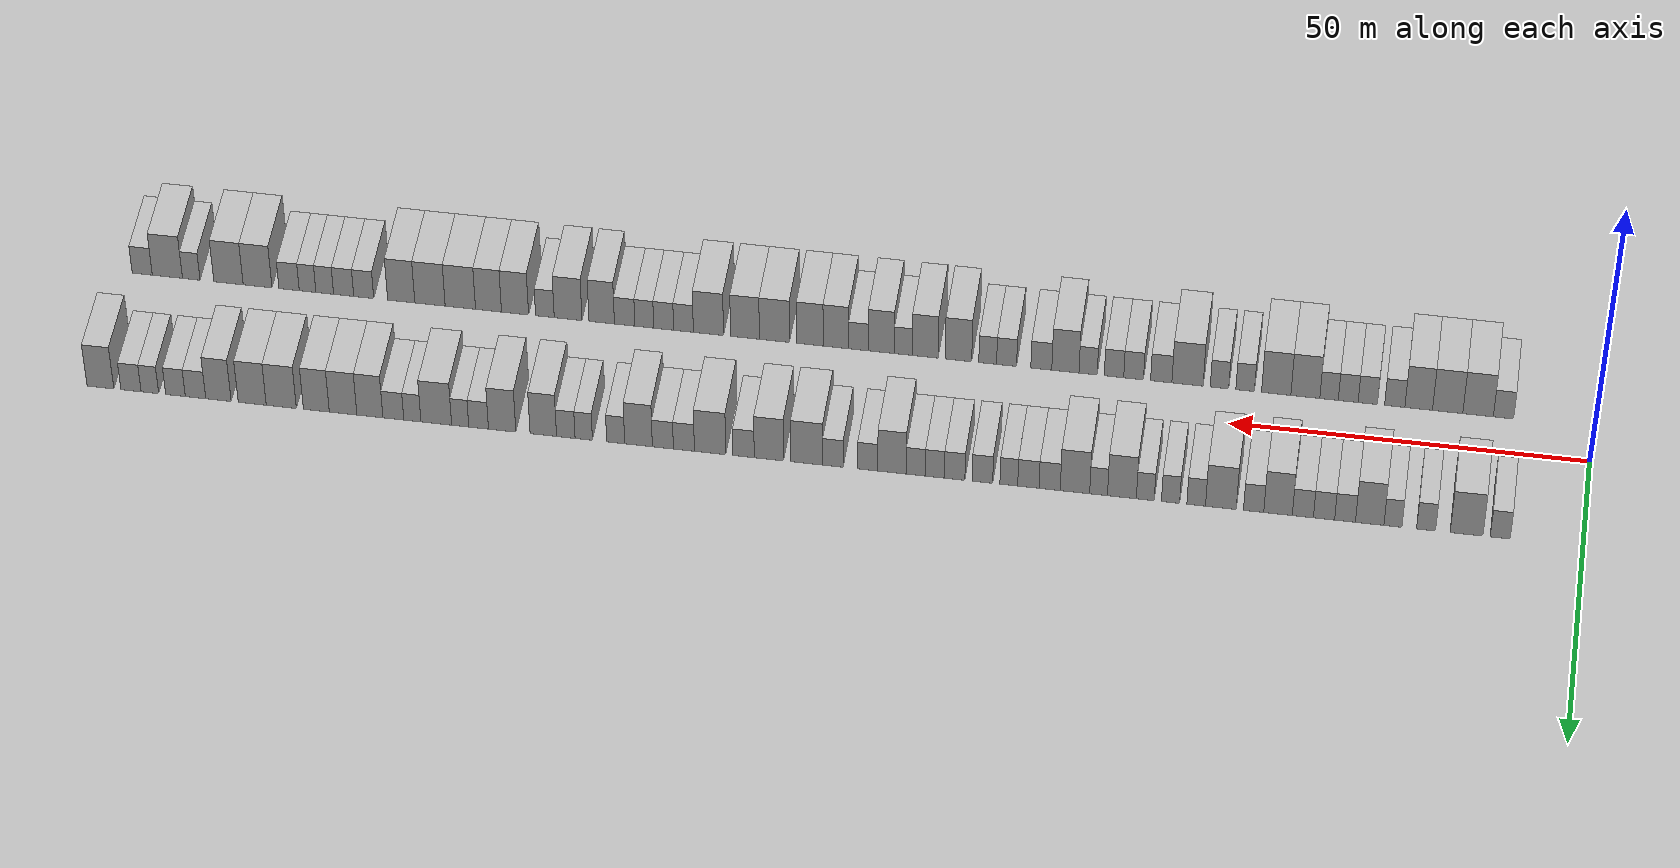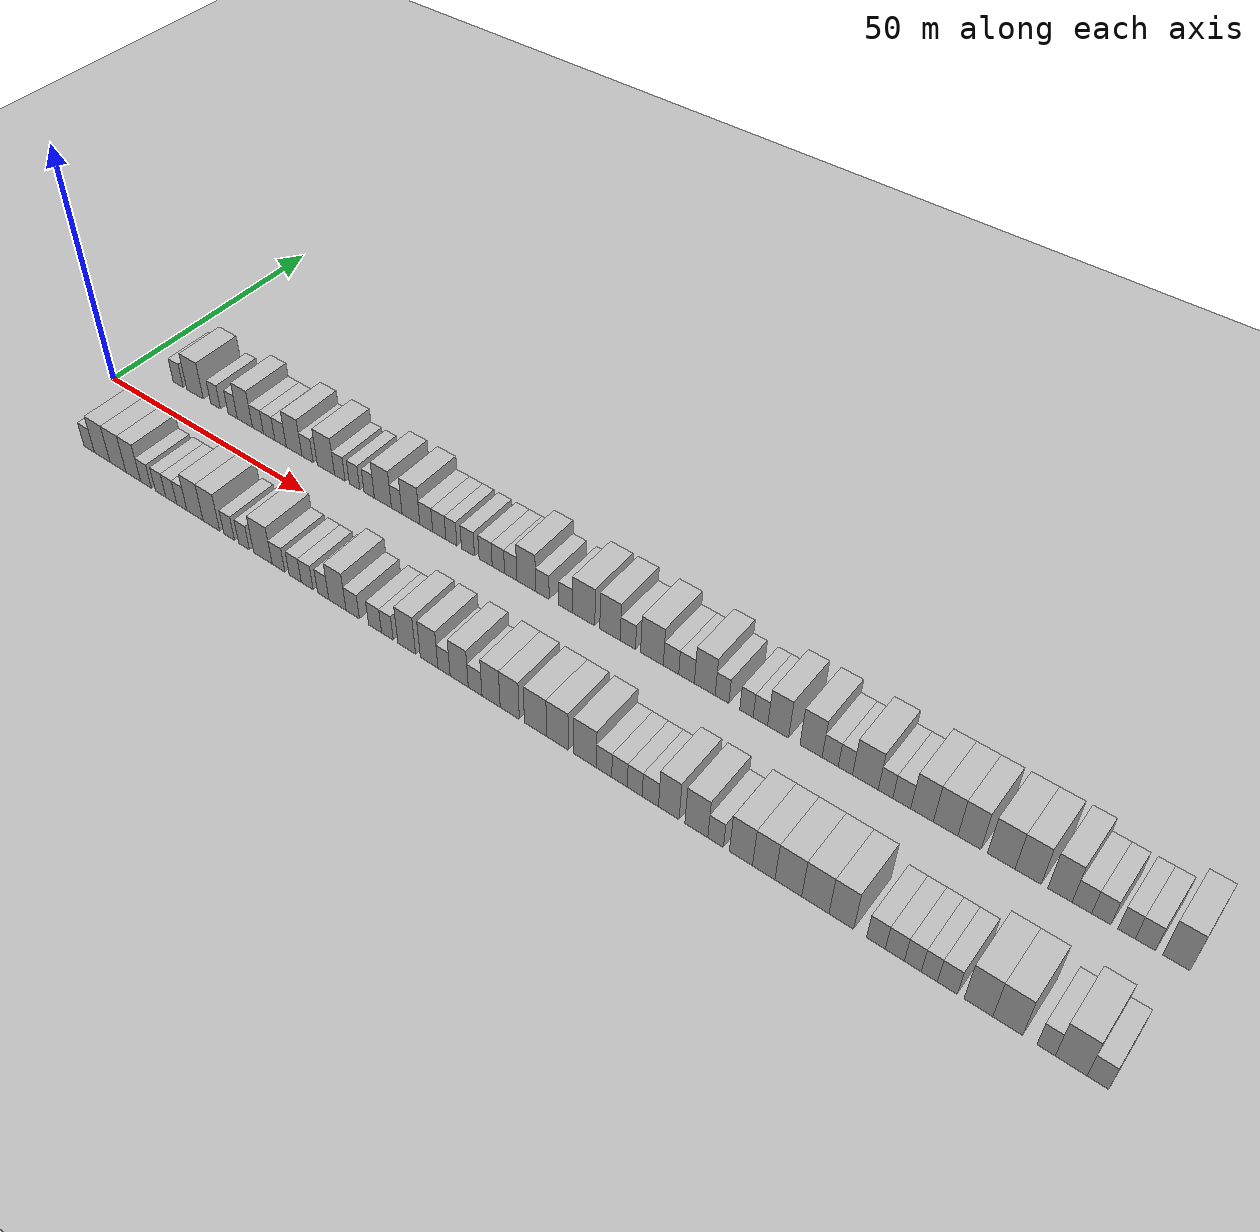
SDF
<?xml version="1.0" encoding="utf-8"?>

<sdf version="1.6">

   <world name="default">

      <gui fullscreen="0">

         <camera name="user_camera">

            <pose>-15 0 4.57585 0 0 0</pose>

            <view_controller>orbit</view_controller>

         </camera>

      </gui>

      <scene>

         <sky>

           <clouds>

             <speed>12</speed>

           </clouds>

         </sky>

         <ambient>0.4 0.4 0.4 1</ambient>

         <background>0.7 0.7 0.7 1</background>

         <shadows>1</shadows>

      </scene>

      <gravity>0 0 -9.8066</gravity>

      <magnetic_field>6e-06 2.3e-05 -4.2e-05</magnetic_field>

      <physics default="0" name="default_physics" type="ode">

         <ode>

            <solver>

               <type>quick</type>

               <iters>10</iters>

               <sor>1.0</sor>

               <use_dynamic_moi_rescaling>0</use_dynamic_moi_rescaling>

            </solver>

            <constraints>

               <cfm>0</cfm>

               <erp>0.2</erp>

               <contact_max_correcting_vel>100</contact_max_correcting_vel>

               <contact_surface_layer>0.001</contact_surface_layer>

            </constraints>

         </ode>

         <max_step_size>0.004</max_step_size>

         <real_time_factor>1</real_time_factor>

         <real_time_update_rate>250</real_time_update_rate>

      </physics>

      <light name="sun" type="directional">

         <cast_shadows>1</cast_shadows>

         <pose>0 0 10 0 0 0</pose>

         <diffuse>0.8 0.8 0.8 1</diffuse>

         <specular>0.2 0.2 0.2 1</specular>

         <attenuation>

            <range>1000</range>

            <constant>0.9</constant>

            <linear>0.01</linear>

            <quadratic>0.001</quadratic>

         </attenuation>

         <direction>-0.5 0.1 -0.9</direction>

      </light>

      <include>

         <name>ground_plane_1</name>

         <uri>model://HANNAS_ground_plane</uri>

         <pose>0 0 0  0 0 0</pose>

      </include>

      <include>

         <name>ground_plane_2</name>

         <uri>model://HANNAS_ground_plane</uri>

         <pose>100 0 0  0 0 0</pose>

      </include>

      <model name="building_1">

         <static>1</static>

         <pose frame="">11.3619 11.0000 0 0.000000 0.000000 1.570796</pose>

         <link name="link">

            <pose frame="">0 0 3.00 0 0 0</pose>

            <collision name="collision">

               <geometry>

                  <box>

                     <size>10.0000 2.7237 6.0000</size>

                  </box>

               </geometry>

               <max_contacts>10</max_contacts>

               <surface>

                  <contact>

                     <ode/>

                  </contact>

                  <bounce/>

                  <friction>

                     <torsional>

                        <ode/>

                     </torsional>

                     <ode/>

                  </friction>

               </surface>

            </collision>

            <visual name="visual">

               <cast_shadows>0</cast_shadows>

               <geometry>

                  <box>

                     <size>10.0000 2.7237 6.0000</size>

                  </box>

               </geometry>

               <material>

                  <script>

                     <uri>model://HANNAS_wall/materials/scripts</uri>

                     <uri>model://HANNAS_wall/materials/textures</uri>

                     <name>vrc/HANNAS_wall</name>

                  </script>

               </material>

            </visual>

            <self_collide>0</self_collide>

            <enable_wind>0</enable_wind>

            <kinematic>0</kinematic>

         </link>

      </model>

      <model name="building_2">

         <static>1</static>

         <pose frame="">15.9564 11.0000 0 0.000000 0.000000 1.570796</pose>

         <link name="link">

            <pose frame="">0 0 4.50 0 0 0</pose>

            <collision name="collision">

               <geometry>

                  <box>

                     <size>10.0000 4.4653 9.0000</size>

                  </box>

               </geometry>

               <max_contacts>10</max_contacts>

               <surface>

                  <contact>

                     <ode/>

                  </contact>

                  <bounce/>

                  <friction>

                     <torsional>

                        <ode/>

                     </torsional>

                     <ode/>

                  </friction>

               </surface>

            </collision>

            <visual name="visual">

               <cast_shadows>0</cast_shadows>

               <geometry>

                  <box>

                     <size>10.0000 4.4653 9.0000</size>

                  </box>

               </geometry>

               <material>

                  <script>

                     <uri>model://HANNAS_wall/materials/scripts</uri>

                     <uri>model://HANNAS_wall/materials/textures</uri>

                     <name>vrc/HANNAS_wall</name>

                  </script>

               </material>

            </visual>

            <self_collide>0</self_collide>

            <enable_wind>0</enable_wind>

            <kinematic>0</kinematic>

         </link>

      </model>

      <model name="building_3">

         <static>1</static>

         <pose frame="">21.4835 11.0000 0 0.000000 0.000000 1.570796</pose>

         <link name="link">

            <pose frame="">0 0 3.00 0 0 0</pose>

            <collision name="collision">

               <geometry>

                  <box>

                     <size>10.0000 2.5890 6.0000</size>

                  </box>

               </geometry>

               <max_contacts>10</max_contacts>

               <surface>

                  <contact>

                     <ode/>

                  </contact>

                  <bounce/>

                  <friction>

                     <torsional>

                        <ode/>

                     </torsional>

                     <ode/>

                  </friction>

               </surface>

            </collision>

            <visual name="visual">

               <cast_shadows>0</cast_shadows>

               <geometry>

                  <box>

                     <size>10.0000 2.5890 6.0000</size>

                  </box>

               </geometry>

               <material>

                  <script>

                     <uri>model://HANNAS_wall/materials/scripts</uri>

                     <uri>model://HANNAS_wall/materials/textures</uri>

                     <name>vrc/HANNAS_wall</name>

                  </script>

               </material>

            </visual>

            <self_collide>0</self_collide>

            <enable_wind>0</enable_wind>

            <kinematic>0</kinematic>

         </link>

      </model>

      <model name="building_4">

         <static>1</static>

         <pose frame="">26.0084 11.0000 0 0.000000 0.000000 1.570796</pose>

         <link name="link">

            <pose frame="">0 0 3.00 0 0 0</pose>

            <collision name="collision">

               <geometry>

                  <box>

                     <size>10.0000 2.4608 6.0000</size>

                  </box>

               </geometry>

               <max_contacts>10</max_contacts>

               <surface>

                  <contact>

                     <ode/>

                  </contact>

                  <bounce/>

                  <friction>

                     <torsional>

                        <ode/>

                     </torsional>

                     <ode/>

                  </friction>

               </surface>

            </collision>

            <visual name="visual">

               <cast_shadows>0</cast_shadows>

               <geometry>

                  <box>

                     <size>10.0000 2.4608 6.0000</size>

                  </box>

               </geometry>

               <material>

                  <script>

                     <uri>model://HANNAS_wall/materials/scripts</uri>

                     <uri>model://HANNAS_wall/materials/textures</uri>

                     <name>vrc/HANNAS_wall</name>

                  </script>

               </material>

            </visual>

            <self_collide>0</self_collide>

            <enable_wind>0</enable_wind>

            <kinematic>0</kinematic>

         </link>

      </model>

      <model name="building_5">

         <static>1</static>

         <pose frame="">29.1895 11.0000 0 0.000000 0.000000 1.570796</pose>

         <link name="link">

            <pose frame="">0 0 4.50 0 0 0</pose>

            <collision name="collision">

               <geometry>

                  <box>

                     <size>10.0000 3.9013 9.0000</size>

                  </box>

               </geometry>

               <max_contacts>10</max_contacts>

               <surface>

                  <contact>

                     <ode/>

                  </contact>

                  <bounce/>

                  <friction>

                     <torsional>

                        <ode/>

                     </torsional>

                     <ode/>

                  </friction>

               </surface>

            </collision>

            <visual name="visual">

               <cast_shadows>0</cast_shadows>

               <geometry>

                  <box>

                     <size>10.0000 3.9013 9.0000</size>

                  </box>

               </geometry>

               <material>

                  <script>

                     <uri>model://HANNAS_wall/materials/scripts</uri>

                     <uri>model://HANNAS_wall/materials/textures</uri>

                     <name>vrc/HANNAS_wall</name>

                  </script>

               </material>

            </visual>

            <self_collide>0</self_collide>

            <enable_wind>0</enable_wind>

            <kinematic>0</kinematic>

         </link>

      </model>

      <model name="building_6">

         <static>1</static>

         <pose frame="">32.5640 11.0000 0 0.000000 0.000000 1.570796</pose>

         <link name="link">

            <pose frame="">0 0 3.00 0 0 0</pose>

            <collision name="collision">

               <geometry>

                  <box>

                     <size>10.0000 2.8478 6.0000</size>

                  </box>

               </geometry>

               <max_contacts>10</max_contacts>

               <surface>

                  <contact>

                     <ode/>

                  </contact>

                  <bounce/>

                  <friction>

                     <torsional>

                        <ode/>

                     </torsional>

                     <ode/>

                  </friction>

               </surface>

            </collision>

            <visual name="visual">

               <cast_shadows>0</cast_shadows>

               <geometry>

                  <box>

                     <size>10.0000 2.8478 6.0000</size>

                  </box>

               </geometry>

               <material>

                  <script>

                     <uri>model://HANNAS_wall/materials/scripts</uri>

                     <uri>model://HANNAS_wall/materials/textures</uri>

                     <name>vrc/HANNAS_wall</name>

                  </script>

               </material>

            </visual>

            <self_collide>0</self_collide>

            <enable_wind>0</enable_wind>

            <kinematic>0</kinematic>

         </link>

      </model>

      <model name="building_7">

         <static>1</static>

         <pose frame="">35.4418 11.0000 0 0.000000 0.000000 1.570796</pose>

         <link name="link">

            <pose frame="">0 0 3.00 0 0 0</pose>

            <collision name="collision">

               <geometry>

                  <box>

                     <size>10.0000 2.9078 6.0000</size>

                  </box>

               </geometry>

               <max_contacts>10</max_contacts>

               <surface>

                  <contact>

                     <ode/>

                  </contact>

                  <bounce/>

                  <friction>

                     <torsional>

                        <ode/>

                     </torsional>

                     <ode/>

                  </friction>

               </surface>

            </collision>

            <visual name="visual">

               <cast_shadows>0</cast_shadows>

               <geometry>

                  <box>

                     <size>10.0000 2.9078 6.0000</size>

                  </box>

               </geometry>

               <material>

                  <script>

                     <uri>model://HANNAS_wall/materials/scripts</uri>

                     <uri>model://HANNAS_wall/materials/textures</uri>

                     <name>vrc/HANNAS_wall</name>

                  </script>

               </material>

            </visual>

            <self_collide>0</self_collide>

            <enable_wind>0</enable_wind>

            <kinematic>0</kinematic>

         </link>

      </model>

      <model name="building_8">

         <static>1</static>

         <pose frame="">38.3424 11.0000 0 0.000000 0.000000 1.570796</pose>

         <link name="link">

            <pose frame="">0 0 3.00 0 0 0</pose>

            <collision name="collision">

               <geometry>

                  <box>

                     <size>10.0000 2.8935 6.0000</size>

                  </box>

               </geometry>

               <max_contacts>10</max_contacts>

               <surface>

                  <contact>

                     <ode/>

                  </contact>

                  <bounce/>

                  <friction>

                     <torsional>

                        <ode/>

                     </torsional>

                     <ode/>

                  </friction>

               </surface>

            </collision>

            <visual name="visual">

               <cast_shadows>0</cast_shadows>

               <geometry>

                  <box>

                     <size>10.0000 2.8935 6.0000</size>

                  </box>

               </geometry>

               <material>

                  <script>

                     <uri>model://HANNAS_wall/materials/scripts</uri>

                     <uri>model://HANNAS_wall/materials/textures</uri>

                     <name>vrc/HANNAS_wall</name>

                  </script>

               </material>

            </visual>

            <self_collide>0</self_collide>

            <enable_wind>0</enable_wind>

            <kinematic>0</kinematic>

         </link>

      </model>

      <model name="building_9">

         <static>1</static>

         <pose frame="">41.7459 11.0000 0 0.000000 0.000000 1.570796</pose>

         <link name="link">

            <pose frame="">0 0 4.50 0 0 0</pose>

            <collision name="collision">

               <geometry>

                  <box>

                     <size>10.0000 3.9136 9.0000</size>

                  </box>

               </geometry>

               <max_contacts>10</max_contacts>

               <surface>

                  <contact>

                     <ode/>

                  </contact>

                  <bounce/>

                  <friction>

                     <torsional>

                        <ode/>

                     </torsional>

                     <ode/>

                  </friction>

               </surface>

            </collision>

            <visual name="visual">

               <cast_shadows>0</cast_shadows>

               <geometry>

                  <box>

                     <size>10.0000 3.9136 9.0000</size>

                  </box>

               </geometry>

               <material>

                  <script>

                     <uri>model://HANNAS_wall/materials/scripts</uri>

                     <uri>model://HANNAS_wall/materials/textures</uri>

                     <name>vrc/HANNAS_wall</name>

                  </script>

               </material>

            </visual>

            <self_collide>0</self_collide>

            <enable_wind>0</enable_wind>

            <kinematic>0</kinematic>

         </link>

      </model>

      <model name="building_10">

         <static>1</static>

         <pose frame="">45.0957 11.0000 0 0.000000 0.000000 1.570796</pose>

         <link name="link">

            <pose frame="">0 0 3.00 0 0 0</pose>

            <collision name="collision">

               <geometry>

                  <box>

                     <size>10.0000 2.7859 6.0000</size>

                  </box>

               </geometry>

               <max_contacts>10</max_contacts>

               <surface>

                  <contact>

                     <ode/>

                  </contact>

                  <bounce/>

                  <friction>

                     <torsional>

                        <ode/>

                     </torsional>

                     <ode/>

                  </friction>

               </surface>

            </collision>

            <visual name="visual">

               <cast_shadows>0</cast_shadows>

               <geometry>

                  <box>

                     <size>10.0000 2.7859 6.0000</size>

                  </box>

               </geometry>

               <material>

                  <script>

                     <uri>model://HANNAS_wall/materials/scripts</uri>

                     <uri>model://HANNAS_wall/materials/textures</uri>

                     <name>vrc/HANNAS_wall</name>

                  </script>

               </material>

            </visual>

            <self_collide>0</self_collide>

            <enable_wind>0</enable_wind>

            <kinematic>0</kinematic>

         </link>

      </model>

      <model name="building_11">

         <static>1</static>

         <pose frame="">49.6018 11.0000 0 0.000000 0.000000 1.570796</pose>

         <link name="link">

            <pose frame="">0 0 4.50 0 0 0</pose>

            <collision name="collision">

               <geometry>

                  <box>

                     <size>10.0000 4.2262 9.0000</size>

                  </box>

               </geometry>

               <max_contacts>10</max_contacts>

               <surface>

                  <contact>

                     <ode/>

                  </contact>

                  <bounce/>

                  <friction>

                     <torsional>

                        <ode/>

                     </torsional>

                     <ode/>

                  </friction>

               </surface>

            </collision>

            <visual name="visual">

               <cast_shadows>0</cast_shadows>

               <geometry>

                  <box>

                     <size>10.0000 4.2262 9.0000</size>

                  </box>

               </geometry>

               <material>

                  <script>

                     <uri>model://HANNAS_wall/materials/scripts</uri>

                     <uri>model://HANNAS_wall/materials/textures</uri>

                     <name>vrc/HANNAS_wall</name>

                  </script>

               </material>

            </visual>

            <self_collide>0</self_collide>

            <enable_wind>0</enable_wind>

            <kinematic>0</kinematic>

         </link>

      </model>

      <model name="building_12">

         <static>1</static>

         <pose frame="">52.9961 11.0000 0 0.000000 0.000000 1.570796</pose>

         <link name="link">

            <pose frame="">0 0 3.00 0 0 0</pose>

            <collision name="collision">

               <geometry>

                  <box>

                     <size>10.0000 2.5625 6.0000</size>

                  </box>

               </geometry>

               <max_contacts>10</max_contacts>

               <surface>

                  <contact>

                     <ode/>

                  </contact>

                  <bounce/>

                  <friction>

                     <torsional>

                        <ode/>

                     </torsional>

                     <ode/>

                  </friction>

               </surface>

            </collision>

            <visual name="visual">

               <cast_shadows>0</cast_shadows>

               <geometry>

                  <box>

                     <size>10.0000 2.5625 6.0000</size>

                  </box>

               </geometry>

               <material>

                  <script>

                     <uri>model://HANNAS_wall/materials/scripts</uri>

                     <uri>model://HANNAS_wall/materials/textures</uri>

                     <name>vrc/HANNAS_wall</name>

                  </script>

               </material>

            </visual>

            <self_collide>0</self_collide>

            <enable_wind>0</enable_wind>

            <kinematic>0</kinematic>

         </link>

      </model>

      <model name="building_13">

         <static>1</static>

         <pose frame="">56.5271 11.0000 0 0.000000 0.000000 1.570796</pose>

         <link name="link">

            <pose frame="">0 0 3.00 0 0 0</pose>

            <collision name="collision">

               <geometry>

                  <box>

                     <size>10.0000 2.4995 6.0000</size>

                  </box>

               </geometry>

               <max_contacts>10</max_contacts>

               <surface>

                  <contact>

                     <ode/>

                  </contact>

                  <bounce/>

                  <friction>

                     <torsional>

                        <ode/>

                     </torsional>

                     <ode/>

                  </friction>

               </surface>

            </collision>

            <visual name="visual">

               <cast_shadows>0</cast_shadows>

               <geometry>

                  <box>

                     <size>10.0000 2.4995 6.0000</size>

                  </box>

               </geometry>

               <material>

                  <script>

                     <uri>model://HANNAS_wall/materials/scripts</uri>

                     <uri>model://HANNAS_wall/materials/textures</uri>

                     <name>vrc/HANNAS_wall</name>

                  </script>

               </material>

            </visual>

            <self_collide>0</self_collide>

            <enable_wind>0</enable_wind>

            <kinematic>0</kinematic>

         </link>

      </model>

      <model name="building_14">

         <static>1</static>

         <pose frame="">60.0050 11.0000 0 0.000000 0.000000 1.570796</pose>

         <link name="link">

            <pose frame="">0 0 3.00 0 0 0</pose>

            <collision name="collision">

               <geometry>

                  <box>

                     <size>10.0000 2.4562 6.0000</size>

                  </box>

               </geometry>

               <max_contacts>10</max_contacts>

               <surface>

                  <contact>

                     <ode/>

                  </contact>

                  <bounce/>

                  <friction>

                     <torsional>

                        <ode/>

                     </torsional>

                     <ode/>

                  </friction>

               </surface>

            </collision>

            <visual name="visual">

               <cast_shadows>0</cast_shadows>

               <geometry>

                  <box>

                     <size>10.0000 2.4562 6.0000</size>

                  </box>

               </geometry>

               <material>

                  <script>

                     <uri>model://HANNAS_wall/materials/scripts</uri>

                     <uri>model://HANNAS_wall/materials/textures</uri>

                     <name>vrc/HANNAS_wall</name>

                  </script>

               </material>

            </visual>

            <self_collide>0</self_collide>

            <enable_wind>0</enable_wind>

            <kinematic>0</kinematic>

         </link>

      </model>

      <model name="building_15">

         <static>1</static>

         <pose frame="">63.2275 11.0000 0 0.000000 0.000000 1.570796</pose>

         <link name="link">

            <pose frame="">0 0 4.50 0 0 0</pose>

            <collision name="collision">

               <geometry>

                  <box>

                     <size>10.0000 3.9888 9.0000</size>

                  </box>

               </geometry>

               <max_contacts>10</max_contacts>

               <surface>

                  <contact>

                     <ode/>

                  </contact>

                  <bounce/>

                  <friction>

                     <torsional>

                        <ode/>

                     </torsional>

                     <ode/>

                  </friction>

               </surface>

            </collision>

            <visual name="visual">

               <cast_shadows>0</cast_shadows>

               <geometry>

                  <box>

                     <size>10.0000 3.9888 9.0000</size>

                  </box>

               </geometry>

               <material>

                  <script>

                     <uri>model://HANNAS_wall/materials/scripts</uri>

                     <uri>model://HANNAS_wall/materials/textures</uri>

                     <name>vrc/HANNAS_wall</name>

                  </script>

               </material>

            </visual>

            <self_collide>0</self_collide>

            <enable_wind>0</enable_wind>

            <kinematic>0</kinematic>

         </link>

      </model>

      <model name="building_16">

         <static>1</static>

         <pose frame="">66.4500 11.0000 0 0.000000 0.000000 1.570796</pose>

         <link name="link">

            <pose frame="">0 0 3.00 0 0 0</pose>

            <collision name="collision">

               <geometry>

                  <box>

                     <size>10.0000 2.4563 6.0000</size>

                  </box>

               </geometry>

               <max_contacts>10</max_contacts>

               <surface>

                  <contact>

                     <ode/>

                  </contact>

                  <bounce/>

                  <friction>

                     <torsional>

                        <ode/>

                     </torsional>

                     <ode/>

                  </friction>

               </surface>

            </collision>

            <visual name="visual">

               <cast_shadows>0</cast_shadows>

               <geometry>

                  <box>

                     <size>10.0000 2.4563 6.0000</size>

                  </box>

               </geometry>

               <material>

                  <script>

                     <uri>model://HANNAS_wall/materials/scripts</uri>

                     <uri>model://HANNAS_wall/materials/textures</uri>

                     <name>vrc/HANNAS_wall</name>

                  </script>

               </material>

            </visual>

            <self_collide>0</self_collide>

            <enable_wind>0</enable_wind>

            <kinematic>0</kinematic>

         </link>

      </model>

      <model name="building_17">

         <static>1</static>

         <pose frame="">69.7121 11.0000 0 0.000000 0.000000 1.570796</pose>

         <link name="link">

            <pose frame="">0 0 4.50 0 0 0</pose>

            <collision name="collision">

               <geometry>

                  <box>

                     <size>10.0000 4.0678 9.0000</size>

                  </box>

               </geometry>

               <max_contacts>10</max_contacts>

               <surface>

                  <contact>

                     <ode/>

                  </contact>

                  <bounce/>

                  <friction>

                     <torsional>

                        <ode/>

                     </torsional>

                     <ode/>

                  </friction>

               </surface>

            </collision>

            <visual name="visual">

               <cast_shadows>0</cast_shadows>

               <geometry>

                  <box>

                     <size>10.0000 4.0678 9.0000</size>

                  </box>

               </geometry>

               <material>

                  <script>

                     <uri>model://HANNAS_wall/materials/scripts</uri>

                     <uri>model://HANNAS_wall/materials/textures</uri>

                     <name>vrc/HANNAS_wall</name>

                  </script>

               </material>

            </visual>

            <self_collide>0</self_collide>

            <enable_wind>0</enable_wind>

            <kinematic>0</kinematic>

         </link>

      </model>

      <model name="building_18">

         <static>1</static>

         <pose frame="">73.2113 11.0000 0 0.000000 0.000000 1.570796</pose>

         <link name="link">

            <pose frame="">0 0 3.00 0 0 0</pose>

            <collision name="collision">

               <geometry>

                  <box>

                     <size>10.0000 2.9305 6.0000</size>

                  </box>

               </geometry>

               <max_contacts>10</max_contacts>

               <surface>

                  <contact>

                     <ode/>

                  </contact>

                  <bounce/>

                  <friction>

                     <torsional>

                        <ode/>

                     </torsional>

                     <ode/>

                  </friction>

               </surface>

            </collision>

            <visual name="visual">

               <cast_shadows>0</cast_shadows>

               <geometry>

                  <box>

                     <size>10.0000 2.9305 6.0000</size>

                  </box>

               </geometry>

               <material>

                  <script>

                     <uri>model://HANNAS_wall/materials/scripts</uri>

                     <uri>model://HANNAS_wall/materials/textures</uri>

                     <name>vrc/HANNAS_wall</name>

                  </script>

               </material>

            </visual>

            <self_collide>0</self_collide>

            <enable_wind>0</enable_wind>

            <kinematic>0</kinematic>

         </link>

      </model>

      <model name="building_19">

         <static>1</static>

         <pose frame="">76.1501 11.0000 0 0.000000 0.000000 1.570796</pose>

         <link name="link">

            <pose frame="">0 0 3.00 0 0 0</pose>

            <collision name="collision">

               <geometry>

                  <box>

                     <size>10.0000 2.9472 6.0000</size>

                  </box>

               </geometry>

               <max_contacts>10</max_contacts>

               <surface>

                  <contact>

                     <ode/>

                  </contact>

                  <bounce/>

                  <friction>

                     <torsional>

                        <ode/>

                     </torsional>

                     <ode/>

                  </friction>

               </surface>

            </collision>

            <visual name="visual">

               <cast_shadows>0</cast_shadows>

               <geometry>

                  <box>

                     <size>10.0000 2.9472 6.0000</size>

                  </box>

               </geometry>

               <material>

                  <script>

                     <uri>model://HANNAS_wall/materials/scripts</uri>

                     <uri>model://HANNAS_wall/materials/textures</uri>

                     <name>vrc/HANNAS_wall</name>

                  </script>

               </material>

            </visual>

            <self_collide>0</self_collide>

            <enable_wind>0</enable_wind>

            <kinematic>0</kinematic>

         </link>

      </model>

      <model name="building_20">

         <static>1</static>

         <pose frame="">78.8567 11.0000 0 0.000000 0.000000 1.570796</pose>

         <link name="link">

            <pose frame="">0 0 3.00 0 0 0</pose>

            <collision name="collision">

               <geometry>

                  <box>

                     <size>10.0000 2.4658 6.0000</size>

                  </box>

               </geometry>

               <max_contacts>10</max_contacts>

               <surface>

                  <contact>

                     <ode/>

                  </contact>

                  <bounce/>

                  <friction>

                     <torsional>

                        <ode/>

                     </torsional>

                     <ode/>

                  </friction>

               </surface>

            </collision>

            <visual name="visual">

               <cast_shadows>0</cast_shadows>

               <geometry>

                  <box>

                     <size>10.0000 2.4658 6.0000</size>

                  </box>

               </geometry>

               <material>

                  <script>

                     <uri>model://HANNAS_wall/materials/scripts</uri>

                     <uri>model://HANNAS_wall/materials/textures</uri>

                     <name>vrc/HANNAS_wall</name>

                  </script>

               </material>

            </visual>

            <self_collide>0</self_collide>

            <enable_wind>0</enable_wind>

            <kinematic>0</kinematic>

         </link>

      </model>

      <model name="building_21">

         <static>1</static>

         <pose frame="">82.5169 11.0000 0 0.000000 0.000000 1.570796</pose>

         <link name="link">

            <pose frame="">0 0 3.00 0 0 0</pose>

            <collision name="collision">

               <geometry>

                  <box>

                     <size>10.0000 2.8547 6.0000</size>

                  </box>

               </geometry>

               <max_contacts>10</max_contacts>

               <surface>

                  <contact>

                     <ode/>

                  </contact>

                  <bounce/>

                  <friction>

                     <torsional>

                        <ode/>

                     </torsional>

                     <ode/>

                  </friction>

               </surface>

            </collision>

            <visual name="visual">

               <cast_shadows>0</cast_shadows>

               <geometry>

                  <box>

                     <size>10.0000 2.8547 6.0000</size>

                  </box>

               </geometry>

               <material>

                  <script>

                     <uri>model://HANNAS_wall/materials/scripts</uri>

                     <uri>model://HANNAS_wall/materials/textures</uri>

                     <name>vrc/HANNAS_wall</name>

                  </script>

               </material>

            </visual>

            <self_collide>0</self_collide>

            <enable_wind>0</enable_wind>

            <kinematic>0</kinematic>

         </link>

      </model>

      <model name="building_22">

         <static>1</static>

         <pose frame="">86.3643 11.0000 0 0.000000 0.000000 1.570796</pose>

         <link name="link">

            <pose frame="">0 0 3.00 0 0 0</pose>

            <collision name="collision">

               <geometry>

                  <box>

                     <size>10.0000 2.8400 6.0000</size>

                  </box>

               </geometry>

               <max_contacts>10</max_contacts>

               <surface>

                  <contact>

                     <ode/>

                  </contact>

                  <bounce/>

                  <friction>

                     <torsional>

                        <ode/>

                     </torsional>

                     <ode/>

                  </friction>

               </surface>

            </collision>

            <visual name="visual">

               <cast_shadows>0</cast_shadows>

               <geometry>

                  <box>

                     <size>10.0000 2.8400 6.0000</size>

                  </box>

               </geometry>

               <material>

                  <script>

                     <uri>model://HANNAS_wall/materials/scripts</uri>

                     <uri>model://HANNAS_wall/materials/textures</uri>

                     <name>vrc/HANNAS_wall</name>

                  </script>

               </material>

            </visual>

            <self_collide>0</self_collide>

            <enable_wind>0</enable_wind>

            <kinematic>0</kinematic>

         </link>

      </model>

      <model name="building_23">

         <static>1</static>

         <pose frame="">89.1174 11.0000 0 0.000000 0.000000 1.570796</pose>

         <link name="link">

            <pose frame="">0 0 3.00 0 0 0</pose>

            <collision name="collision">

               <geometry>

                  <box>

                     <size>10.0000 2.6662 6.0000</size>

                  </box>

               </geometry>

               <max_contacts>10</max_contacts>

               <surface>

                  <contact>

                     <ode/>

                  </contact>

                  <bounce/>

                  <friction>

                     <torsional>

                        <ode/>

                     </torsional>

                     <ode/>

                  </friction>

               </surface>

            </collision>

            <visual name="visual">

               <cast_shadows>0</cast_shadows>

               <geometry>

                  <box>

                     <size>10.0000 2.6662 6.0000</size>

                  </box>

               </geometry>

               <material>

                  <script>

                     <uri>model://HANNAS_wall/materials/scripts</uri>

                     <uri>model://HANNAS_wall/materials/textures</uri>

                     <name>vrc/HANNAS_wall</name>

                  </script>

               </material>

            </visual>

            <self_collide>0</self_collide>

            <enable_wind>0</enable_wind>

            <kinematic>0</kinematic>

         </link>

      </model>

      <model name="building_24">

         <static>1</static>

         <pose frame="">91.7686 11.0000 0 0.000000 0.000000 1.570796</pose>

         <link name="link">

            <pose frame="">0 0 3.00 0 0 0</pose>

            <collision name="collision">

               <geometry>

                  <box>

                     <size>10.0000 2.6361 6.0000</size>

                  </box>

               </geometry>

               <max_contacts>10</max_contacts>

               <surface>

                  <contact>

                     <ode/>

                  </contact>

                  <bounce/>

                  <friction>

                     <torsional>

                        <ode/>

                     </torsional>

                     <ode/>

                  </friction>

               </surface>

            </collision>

            <visual name="visual">

               <cast_shadows>0</cast_shadows>

               <geometry>

                  <box>

                     <size>10.0000 2.6361 6.0000</size>

                  </box>

               </geometry>

               <material>

                  <script>

                     <uri>model://HANNAS_wall/materials/scripts</uri>

                     <uri>model://HANNAS_wall/materials/textures</uri>

                     <name>vrc/HANNAS_wall</name>

                  </script>

               </material>

            </visual>

            <self_collide>0</self_collide>

            <enable_wind>0</enable_wind>

            <kinematic>0</kinematic>

         </link>

      </model>

      <model name="building_25">

         <static>1</static>

         <pose frame="">95.0623 11.0000 0 0.000000 0.000000 1.570796</pose>

         <link name="link">

            <pose frame="">0 0 4.50 0 0 0</pose>

            <collision name="collision">

               <geometry>

                  <box>

                     <size>10.0000 3.9512 9.0000</size>

                  </box>

               </geometry>

               <max_contacts>10</max_contacts>

               <surface>

                  <contact>

                     <ode/>

                  </contact>

                  <bounce/>

                  <friction>

                     <torsional>

                        <ode/>

                     </torsional>

                     <ode/>

                  </friction>

               </surface>

            </collision>

            <visual name="visual">

               <cast_shadows>0</cast_shadows>

               <geometry>

                  <box>

                     <size>10.0000 3.9512 9.0000</size>

                  </box>

               </geometry>

               <material>

                  <script>

                     <uri>model://HANNAS_wall/materials/scripts</uri>

                     <uri>model://HANNAS_wall/materials/textures</uri>

                     <name>vrc/HANNAS_wall</name>

                  </script>

               </material>

            </visual>

            <self_collide>0</self_collide>

            <enable_wind>0</enable_wind>

            <kinematic>0</kinematic>

         </link>

      </model>

      <model name="building_26">

         <static>1</static>

         <pose frame="">98.4367 11.0000 0 0.000000 0.000000 1.570796</pose>

         <link name="link">

            <pose frame="">0 0 3.00 0 0 0</pose>

            <collision name="collision">

               <geometry>

                  <box>

                     <size>10.0000 2.7976 6.0000</size>

                  </box>

               </geometry>

               <max_contacts>10</max_contacts>

               <surface>

                  <contact>

                     <ode/>

                  </contact>

                  <bounce/>

                  <friction>

                     <torsional>

                        <ode/>

                     </torsional>

                     <ode/>

                  </friction>

               </surface>

            </collision>

            <visual name="visual">

               <cast_shadows>0</cast_shadows>

               <geometry>

                  <box>

                     <size>10.0000 2.7976 6.0000</size>

                  </box>

               </geometry>

               <material>

                  <script>

                     <uri>model://HANNAS_wall/materials/scripts</uri>

                     <uri>model://HANNAS_wall/materials/textures</uri>

                     <name>vrc/HANNAS_wall</name>

                  </script>

               </material>

            </visual>

            <self_collide>0</self_collide>

            <enable_wind>0</enable_wind>

            <kinematic>0</kinematic>

         </link>

      </model>

      <model name="building_27">

         <static>1</static>

         <pose frame="">103.2614 11.0000 0 0.000000 0.000000 1.570796</pose>

         <link name="link">

            <pose frame="">0 0 3.00 0 0 0</pose>

            <collision name="collision">

               <geometry>

                  <box>

                     <size>10.0000 2.8519 6.0000</size>

                  </box>

               </geometry>

               <max_contacts>10</max_contacts>

               <surface>

                  <contact>

                     <ode/>

                  </contact>

                  <bounce/>

                  <friction>

                     <torsional>

                        <ode/>

                     </torsional>

                     <ode/>

                  </friction>

               </surface>

            </collision>

            <visual name="visual">

               <cast_shadows>0</cast_shadows>

               <geometry>

                  <box>

                     <size>10.0000 2.8519 6.0000</size>

                  </box>

               </geometry>

               <material>

                  <script>

                     <uri>model://HANNAS_wall/materials/scripts</uri>

                     <uri>model://HANNAS_wall/materials/textures</uri>

                     <name>vrc/HANNAS_wall</name>

                  </script>

               </material>

            </visual>

            <self_collide>0</self_collide>

            <enable_wind>0</enable_wind>

            <kinematic>0</kinematic>

         </link>

      </model>

      <model name="building_28">

         <static>1</static>

         <pose frame="">106.9206 11.0000 0 0.000000 0.000000 1.570796</pose>

         <link name="link">

            <pose frame="">0 0 4.50 0 0 0</pose>

            <collision name="collision">

               <geometry>

                  <box>

                     <size>10.0000 4.4664 9.0000</size>

                  </box>

               </geometry>

               <max_contacts>10</max_contacts>

               <surface>

                  <contact>

                     <ode/>

                  </contact>

                  <bounce/>

                  <friction>

                     <torsional>

                        <ode/>

                     </torsional>

                     <ode/>

                  </friction>

               </surface>

            </collision>

            <visual name="visual">

               <cast_shadows>0</cast_shadows>

               <geometry>

                  <box>

                     <size>10.0000 4.4664 9.0000</size>

                  </box>

               </geometry>

               <material>

                  <script>

                     <uri>model://HANNAS_wall/materials/scripts</uri>

                     <uri>model://HANNAS_wall/materials/textures</uri>

                     <name>vrc/HANNAS_wall</name>

                  </script>

               </material>

            </visual>

            <self_collide>0</self_collide>

            <enable_wind>0</enable_wind>

            <kinematic>0</kinematic>

         </link>

      </model>

      <model name="building_29">

         <static>1</static>

         <pose frame="">112.1940 11.0000 0 0.000000 0.000000 1.570796</pose>

         <link name="link">

            <pose frame="">0 0 4.50 0 0 0</pose>

            <collision name="collision">

               <geometry>

                  <box>

                     <size>10.0000 4.0805 9.0000</size>

                  </box>

               </geometry>

               <max_contacts>10</max_contacts>

               <surface>

                  <contact>

                     <ode/>

                  </contact>

                  <bounce/>

                  <friction>

                     <torsional>

                        <ode/>

                     </torsional>

                     <ode/>

                  </friction>

               </surface>

            </collision>

            <visual name="visual">

               <cast_shadows>0</cast_shadows>

               <geometry>

                  <box>

                     <size>10.0000 4.0805 9.0000</size>

                  </box>

               </geometry>

               <material>

                  <script>

                     <uri>model://HANNAS_wall/materials/scripts</uri>

                     <uri>model://HANNAS_wall/materials/textures</uri>

                     <name>vrc/HANNAS_wall</name>

                  </script>

               </material>

            </visual>

            <self_collide>0</self_collide>

            <enable_wind>0</enable_wind>

            <kinematic>0</kinematic>

         </link>

      </model>

      <model name="building_30">

         <static>1</static>

         <pose frame="">115.7216 11.0000 0 0.000000 0.000000 1.570796</pose>

         <link name="link">

            <pose frame="">0 0 3.00 0 0 0</pose>

            <collision name="collision">

               <geometry>

                  <box>

                     <size>10.0000 2.9746 6.0000</size>

                  </box>

               </geometry>

               <max_contacts>10</max_contacts>

               <surface>

                  <contact>

                     <ode/>

                  </contact>

                  <bounce/>

                  <friction>

                     <torsional>

                        <ode/>

                     </torsional>

                     <ode/>

                  </friction>

               </surface>

            </collision>

            <visual name="visual">

               <cast_shadows>0</cast_shadows>

               <geometry>

                  <box>

                     <size>10.0000 2.9746 6.0000</size>

                  </box>

               </geometry>

               <material>

                  <script>

                     <uri>model://HANNAS_wall/materials/scripts</uri>

                     <uri>model://HANNAS_wall/materials/textures</uri>

                     <name>vrc/HANNAS_wall</name>

                  </script>

               </material>

            </visual>

            <self_collide>0</self_collide>

            <enable_wind>0</enable_wind>

            <kinematic>0</kinematic>

         </link>

      </model>

      <model name="building_31">

         <static>1</static>

         <pose frame="">120.4012 11.0000 0 0.000000 0.000000 1.570796</pose>

         <link name="link">

            <pose frame="">0 0 4.50 0 0 0</pose>

            <collision name="collision">

               <geometry>

                  <box>

                     <size>10.0000 4.3846 9.0000</size>

                  </box>

               </geometry>

               <max_contacts>10</max_contacts>

               <surface>

                  <contact>

                     <ode/>

                  </contact>

                  <bounce/>

                  <friction>

                     <torsional>

                        <ode/>

                     </torsional>

                     <ode/>

                  </friction>

               </surface>

            </collision>

            <visual name="visual">

               <cast_shadows>0</cast_shadows>

               <geometry>

                  <box>

                     <size>10.0000 4.3846 9.0000</size>

                  </box>

               </geometry>

               <material>

                  <script>

                     <uri>model://HANNAS_wall/materials/scripts</uri>

                     <uri>model://HANNAS_wall/materials/textures</uri>

                     <name>vrc/HANNAS_wall</name>

                  </script>

               </material>

            </visual>

            <self_collide>0</self_collide>

            <enable_wind>0</enable_wind>

            <kinematic>0</kinematic>

         </link>

      </model>

      <model name="building_32">

         <static>1</static>

         <pose frame="">124.0630 11.0000 0 0.000000 0.000000 1.570796</pose>

         <link name="link">

            <pose frame="">0 0 3.00 0 0 0</pose>

            <collision name="collision">

               <geometry>

                  <box>

                     <size>10.0000 2.9389 6.0000</size>

                  </box>

               </geometry>

               <max_contacts>10</max_contacts>

               <surface>

                  <contact>

                     <ode/>

                  </contact>

                  <bounce/>

                  <friction>

                     <torsional>

                        <ode/>

                     </torsional>

                     <ode/>

                  </friction>

               </surface>

            </collision>

            <visual name="visual">

               <cast_shadows>0</cast_shadows>

               <geometry>

                  <box>

                     <size>10.0000 2.9389 6.0000</size>

                  </box>

               </geometry>

               <material>

                  <script>

                     <uri>model://HANNAS_wall/materials/scripts</uri>

                     <uri>model://HANNAS_wall/materials/textures</uri>

                     <name>vrc/HANNAS_wall</name>

                  </script>

               </material>

            </visual>

            <self_collide>0</self_collide>

            <enable_wind>0</enable_wind>

            <kinematic>0</kinematic>

         </link>

      </model>

      <model name="building_33">

         <static>1</static>

         <pose frame="">127.0050 11.0000 0 0.000000 0.000000 1.570796</pose>

         <link name="link">

            <pose frame="">0 0 3.00 0 0 0</pose>

            <collision name="collision">

               <geometry>

                  <box>

                     <size>10.0000 2.9452 6.0000</size>

                  </box>

               </geometry>

               <max_contacts>10</max_contacts>

               <surface>

                  <contact>

                     <ode/>

                  </contact>

                  <bounce/>

                  <friction>

                     <torsional>

                        <ode/>

                     </torsional>

                     <ode/>

                  </friction>

               </surface>

            </collision>

            <visual name="visual">

               <cast_shadows>0</cast_shadows>

               <geometry>

                  <box>

                     <size>10.0000 2.9452 6.0000</size>

                  </box>

               </geometry>

               <material>

                  <script>

                     <uri>model://HANNAS_wall/materials/scripts</uri>

                     <uri>model://HANNAS_wall/materials/textures</uri>

                     <name>vrc/HANNAS_wall</name>

                  </script>

               </material>

            </visual>

            <self_collide>0</self_collide>

            <enable_wind>0</enable_wind>

            <kinematic>0</kinematic>

         </link>

      </model>

      <model name="building_34">

         <static>1</static>

         <pose frame="">130.4113 11.0000 0 0.000000 0.000000 1.570796</pose>

         <link name="link">

            <pose frame="">0 0 4.50 0 0 0</pose>

            <collision name="collision">

               <geometry>

                  <box>

                     <size>10.0000 3.8673 9.0000</size>

                  </box>

               </geometry>

               <max_contacts>10</max_contacts>

               <surface>

                  <contact>

                     <ode/>

                  </contact>

                  <bounce/>

                  <friction>

                     <torsional>

                        <ode/>

                     </torsional>

                     <ode/>

                  </friction>

               </surface>

            </collision>

            <visual name="visual">

               <cast_shadows>0</cast_shadows>

               <geometry>

                  <box>

                     <size>10.0000 3.8673 9.0000</size>

                  </box>

               </geometry>

               <material>

                  <script>

                     <uri>model://HANNAS_wall/materials/scripts</uri>

                     <uri>model://HANNAS_wall/materials/textures</uri>

                     <name>vrc/HANNAS_wall</name>

                  </script>

               </material>

            </visual>

            <self_collide>0</self_collide>

            <enable_wind>0</enable_wind>

            <kinematic>0</kinematic>

         </link>

      </model>

      <model name="building_35">

         <static>1</static>

         <pose frame="">133.6094 11.0000 0 0.000000 0.000000 1.570796</pose>

         <link name="link">

            <pose frame="">0 0 3.00 0 0 0</pose>

            <collision name="collision">

               <geometry>

                  <box>

                     <size>10.0000 2.5289 6.0000</size>

                  </box>

               </geometry>

               <max_contacts>10</max_contacts>

               <surface>

                  <contact>

                     <ode/>

                  </contact>

                  <bounce/>

                  <friction>

                     <torsional>

                        <ode/>

                     </torsional>

                     <ode/>

                  </friction>

               </surface>

            </collision>

            <visual name="visual">

               <cast_shadows>0</cast_shadows>

               <geometry>

                  <box>

                     <size>10.0000 2.5289 6.0000</size>

                  </box>

               </geometry>

               <material>

                  <script>

                     <uri>model://HANNAS_wall/materials/scripts</uri>

                     <uri>model://HANNAS_wall/materials/textures</uri>

                     <name>vrc/HANNAS_wall</name>

                  </script>

               </material>

            </visual>

            <self_collide>0</self_collide>

            <enable_wind>0</enable_wind>

            <kinematic>0</kinematic>

         </link>

      </model>

      <model name="building_36">

         <static>1</static>

         <pose frame="">138.0905 11.0000 0 0.000000 0.000000 1.570796</pose>

         <link name="link">

            <pose frame="">0 0 3.00 0 0 0</pose>

            <collision name="collision">

               <geometry>

                  <box>

                     <size>10.0000 2.4332 6.0000</size>

                  </box>

               </geometry>

               <max_contacts>10</max_contacts>

               <surface>

                  <contact>

                     <ode/>

                  </contact>

                  <bounce/>

                  <friction>

                     <torsional>

                        <ode/>

                     </torsional>

                     <ode/>

                  </friction>

               </surface>

            </collision>

            <visual name="visual">

               <cast_shadows>0</cast_shadows>

               <geometry>

                  <box>

                     <size>10.0000 2.4332 6.0000</size>

                  </box>

               </geometry>

               <material>

                  <script>

                     <uri>model://HANNAS_wall/materials/scripts</uri>

                     <uri>model://HANNAS_wall/materials/textures</uri>

                     <name>vrc/HANNAS_wall</name>

                  </script>

               </material>

            </visual>

            <self_collide>0</self_collide>

            <enable_wind>0</enable_wind>

            <kinematic>0</kinematic>

         </link>

      </model>

      <model name="building_37">

         <static>1</static>

         <pose frame="">140.6060 11.0000 0 0.000000 0.000000 1.570796</pose>

         <link name="link">

            <pose frame="">0 0 3.00 0 0 0</pose>

            <collision name="collision">

               <geometry>

                  <box>

                     <size>10.0000 2.5978 6.0000</size>

                  </box>

               </geometry>

               <max_contacts>10</max_contacts>

               <surface>

                  <contact>

                     <ode/>

                  </contact>

                  <bounce/>

                  <friction>

                     <torsional>

                        <ode/>

                     </torsional>

                     <ode/>

                  </friction>

               </surface>

            </collision>

            <visual name="visual">

               <cast_shadows>0</cast_shadows>

               <geometry>

                  <box>

                     <size>10.0000 2.5978 6.0000</size>

                  </box>

               </geometry>

               <material>

                  <script>

                     <uri>model://HANNAS_wall/materials/scripts</uri>

                     <uri>model://HANNAS_wall/materials/textures</uri>

                     <name>vrc/HANNAS_wall</name>

                  </script>

               </material>

            </visual>

            <self_collide>0</self_collide>

            <enable_wind>0</enable_wind>

            <kinematic>0</kinematic>

         </link>

      </model>

      <model name="building_38">

         <static>1</static>

         <pose frame="">143.7648 11.0000 0 0.000000 0.000000 1.570796</pose>

         <link name="link">

            <pose frame="">0 0 4.50 0 0 0</pose>

            <collision name="collision">

               <geometry>

                  <box>

                     <size>10.0000 3.7199 9.0000</size>

                  </box>

               </geometry>

               <max_contacts>10</max_contacts>

               <surface>

                  <contact>

                     <ode/>

                  </contact>

                  <bounce/>

                  <friction>

                     <torsional>

                        <ode/>

                     </torsional>

                     <ode/>

                  </friction>

               </surface>

            </collision>

            <visual name="visual">

               <cast_shadows>0</cast_shadows>

               <geometry>

                  <box>

                     <size>10.0000 3.7199 9.0000</size>

                  </box>

               </geometry>

               <material>

                  <script>

                     <uri>model://HANNAS_wall/materials/scripts</uri>

                     <uri>model://HANNAS_wall/materials/textures</uri>

                     <name>vrc/HANNAS_wall</name>

                  </script>

               </material>

            </visual>

            <self_collide>0</self_collide>

            <enable_wind>0</enable_wind>

            <kinematic>0</kinematic>

         </link>

      </model>

      <model name="building_39">

         <static>1</static>

         <pose frame="">149.5519 11.0000 0 0.000000 0.000000 1.570796</pose>

         <link name="link">

            <pose frame="">0 0 4.50 0 0 0</pose>

            <collision name="collision">

               <geometry>

                  <box>

                     <size>10.0000 3.8543 9.0000</size>

                  </box>

               </geometry>

               <max_contacts>10</max_contacts>

               <surface>

                  <contact>

                     <ode/>

                  </contact>

                  <bounce/>

                  <friction>

                     <torsional>

                        <ode/>

                     </torsional>

                     <ode/>

                  </friction>

               </surface>

            </collision>

            <visual name="visual">

               <cast_shadows>0</cast_shadows>

               <geometry>

                  <box>

                     <size>10.0000 3.8543 9.0000</size>

                  </box>

               </geometry>

               <material>

                  <script>

                     <uri>model://HANNAS_wall/materials/scripts</uri>

                     <uri>model://HANNAS_wall/materials/textures</uri>

                     <name>vrc/HANNAS_wall</name>

                  </script>

               </material>

            </visual>

            <self_collide>0</self_collide>

            <enable_wind>0</enable_wind>

            <kinematic>0</kinematic>

         </link>

      </model>

      <model name="building_40">

         <static>1</static>

         <pose frame="">152.8658 11.0000 0 0.000000 0.000000 1.570796</pose>

         <link name="link">

            <pose frame="">0 0 3.00 0 0 0</pose>

            <collision name="collision">

               <geometry>

                  <box>

                     <size>10.0000 2.7734 6.0000</size>

                  </box>

               </geometry>

               <max_contacts>10</max_contacts>

               <surface>

                  <contact>

                     <ode/>

                  </contact>

                  <bounce/>

                  <friction>

                     <torsional>

                        <ode/>

                     </torsional>

                     <ode/>

                  </friction>

               </surface>

            </collision>

            <visual name="visual">

               <cast_shadows>0</cast_shadows>

               <geometry>

                  <box>

                     <size>10.0000 2.7734 6.0000</size>

                  </box>

               </geometry>

               <material>

                  <script>

                     <uri>model://HANNAS_wall/materials/scripts</uri>

                     <uri>model://HANNAS_wall/materials/textures</uri>

                     <name>vrc/HANNAS_wall</name>

                  </script>

               </material>

            </visual>

            <self_collide>0</self_collide>

            <enable_wind>0</enable_wind>

            <kinematic>0</kinematic>

         </link>

      </model>

      <model name="building_41">

         <static>1</static>

         <pose frame="">155.4579 11.0000 0 0.000000 0.000000 1.570796</pose>

         <link name="link">

            <pose frame="">0 0 3.00 0 0 0</pose>

            <collision name="collision">

               <geometry>

                  <box>

                     <size>10.0000 2.4107 6.0000</size>

                  </box>

               </geometry>

               <max_contacts>10</max_contacts>

               <surface>

                  <contact>

                     <ode/>

                  </contact>

                  <bounce/>

                  <friction>

                     <torsional>

                        <ode/>

                     </torsional>

                     <ode/>

                  </friction>

               </surface>

            </collision>

            <visual name="visual">

               <cast_shadows>0</cast_shadows>

               <geometry>

                  <box>

                     <size>10.0000 2.4107 6.0000</size>

                  </box>

               </geometry>

               <material>

                  <script>

                     <uri>model://HANNAS_wall/materials/scripts</uri>

                     <uri>model://HANNAS_wall/materials/textures</uri>

                     <name>vrc/HANNAS_wall</name>

                  </script>

               </material>

            </visual>

            <self_collide>0</self_collide>

            <enable_wind>0</enable_wind>

            <kinematic>0</kinematic>

         </link>

      </model>

      <model name="building_42">

         <static>1</static>

         <pose frame="">158.8266 11.0000 0 0.000000 0.000000 1.570796</pose>

         <link name="link">

            <pose frame="">0 0 4.50 0 0 0</pose>

            <collision name="collision">

               <geometry>

                  <box>

                     <size>10.0000 4.3266 9.0000</size>

                  </box>

               </geometry>

               <max_contacts>10</max_contacts>

               <surface>

                  <contact>

                     <ode/>

                  </contact>

                  <bounce/>

                  <friction>

                     <torsional>

                        <ode/>

                     </torsional>

                     <ode/>

                  </friction>

               </surface>

            </collision>

            <visual name="visual">

               <cast_shadows>0</cast_shadows>

               <geometry>

                  <box>

                     <size>10.0000 4.3266 9.0000</size>

                  </box>

               </geometry>

               <material>

                  <script>

                     <uri>model://HANNAS_wall/materials/scripts</uri>

                     <uri>model://HANNAS_wall/materials/textures</uri>

                     <name>vrc/HANNAS_wall</name>

                  </script>

               </material>

            </visual>

            <self_collide>0</self_collide>

            <enable_wind>0</enable_wind>

            <kinematic>0</kinematic>

         </link>

      </model>

      <model name="building_43">

         <static>1</static>

         <pose frame="">162.2011 11.0000 0 0.000000 0.000000 1.570796</pose>

         <link name="link">

            <pose frame="">0 0 3.00 0 0 0</pose>

            <collision name="collision">

               <geometry>

                  <box>

                     <size>10.0000 2.4226 6.0000</size>

                  </box>

               </geometry>

               <max_contacts>10</max_contacts>

               <surface>

                  <contact>

                     <ode/>

                  </contact>

                  <bounce/>

                  <friction>

                     <torsional>

                        <ode/>

                     </torsional>

                     <ode/>

                  </friction>

               </surface>

            </collision>

            <visual name="visual">

               <cast_shadows>0</cast_shadows>

               <geometry>

                  <box>

                     <size>10.0000 2.4226 6.0000</size>

                  </box>

               </geometry>

               <material>

                  <script>

                     <uri>model://HANNAS_wall/materials/scripts</uri>

                     <uri>model://HANNAS_wall/materials/textures</uri>

                     <name>vrc/HANNAS_wall</name>

                  </script>

               </material>

            </visual>

            <self_collide>0</self_collide>

            <enable_wind>0</enable_wind>

            <kinematic>0</kinematic>

         </link>

      </model>

      <model name="building_44">

         <static>1</static>

         <pose frame="">164.8834 11.0000 0 0.000000 0.000000 1.570796</pose>

         <link name="link">

            <pose frame="">0 0 3.00 0 0 0</pose>

            <collision name="collision">

               <geometry>

                  <box>

                     <size>10.0000 2.9419 6.0000</size>

                  </box>

               </geometry>

               <max_contacts>10</max_contacts>

               <surface>

                  <contact>

                     <ode/>

                  </contact>

                  <bounce/>

                  <friction>

                     <torsional>

                        <ode/>

                     </torsional>

                     <ode/>

                  </friction>

               </surface>

            </collision>

            <visual name="visual">

               <cast_shadows>0</cast_shadows>

               <geometry>

                  <box>

                     <size>10.0000 2.9419 6.0000</size>

                  </box>

               </geometry>

               <material>

                  <script>

                     <uri>model://HANNAS_wall/materials/scripts</uri>

                     <uri>model://HANNAS_wall/materials/textures</uri>

                     <name>vrc/HANNAS_wall</name>

                  </script>

               </material>

            </visual>

            <self_collide>0</self_collide>

            <enable_wind>0</enable_wind>

            <kinematic>0</kinematic>

         </link>

      </model>

      <model name="building_45">

         <static>1</static>

         <pose frame="">168.1910 11.0000 0 0.000000 0.000000 1.570796</pose>

         <link name="link">

            <pose frame="">0 0 4.50 0 0 0</pose>

            <collision name="collision">

               <geometry>

                  <box>

                     <size>10.0000 3.6733 9.0000</size>

                  </box>

               </geometry>

               <max_contacts>10</max_contacts>

               <surface>

                  <contact>

                     <ode/>

                  </contact>

                  <bounce/>

                  <friction>

                     <torsional>

                        <ode/>

                     </torsional>

                     <ode/>

                  </friction>

               </surface>

            </collision>

            <visual name="visual">

               <cast_shadows>0</cast_shadows>

               <geometry>

                  <box>

                     <size>10.0000 3.6733 9.0000</size>

                  </box>

               </geometry>

               <material>

                  <script>

                     <uri>model://HANNAS_wall/materials/scripts</uri>

                     <uri>model://HANNAS_wall/materials/textures</uri>

                     <name>vrc/HANNAS_wall</name>

                  </script>

               </material>

            </visual>

            <self_collide>0</self_collide>

            <enable_wind>0</enable_wind>

            <kinematic>0</kinematic>

         </link>

      </model>

      <model name="building_46">

         <static>1</static>

         <pose frame="">171.9816 11.0000 0 0.000000 0.000000 1.570796</pose>

         <link name="link">

            <pose frame="">0 0 4.50 0 0 0</pose>

            <collision name="collision">

               <geometry>

                  <box>

                     <size>10.0000 3.9079 9.0000</size>

                  </box>

               </geometry>

               <max_contacts>10</max_contacts>

               <surface>

                  <contact>

                     <ode/>

                  </contact>

                  <bounce/>

                  <friction>

                     <torsional>

                        <ode/>

                     </torsional>

                     <ode/>

                  </friction>

               </surface>

            </collision>

            <visual name="visual">

               <cast_shadows>0</cast_shadows>

               <geometry>

                  <box>

                     <size>10.0000 3.9079 9.0000</size>

                  </box>

               </geometry>

               <material>

                  <script>

                     <uri>model://HANNAS_wall/materials/scripts</uri>

                     <uri>model://HANNAS_wall/materials/textures</uri>

                     <name>vrc/HANNAS_wall</name>

                  </script>

               </material>

            </visual>

            <self_collide>0</self_collide>

            <enable_wind>0</enable_wind>

            <kinematic>0</kinematic>

         </link>

      </model>

      <model name="building_47">

         <static>1</static>

         <pose frame="">175.7639 11.0000 0 0.000000 0.000000 1.570796</pose>

         <link name="link">

            <pose frame="">0 0 4.50 0 0 0</pose>

            <collision name="collision">

               <geometry>

                  <box>

                     <size>10.0000 3.6567 9.0000</size>

                  </box>

               </geometry>

               <max_contacts>10</max_contacts>

               <surface>

                  <contact>

                     <ode/>

                  </contact>

                  <bounce/>

                  <friction>

                     <torsional>

                        <ode/>

                     </torsional>

                     <ode/>

                  </friction>

               </surface>

            </collision>

            <visual name="visual">

               <cast_shadows>0</cast_shadows>

               <geometry>

                  <box>

                     <size>10.0000 3.6567 9.0000</size>

                  </box>

               </geometry>

               <material>

                  <script>

                     <uri>model://HANNAS_wall/materials/scripts</uri>

                     <uri>model://HANNAS_wall/materials/textures</uri>

                     <name>vrc/HANNAS_wall</name>

                  </script>

               </material>

            </visual>

            <self_collide>0</self_collide>

            <enable_wind>0</enable_wind>

            <kinematic>0</kinematic>

         </link>

      </model>

      <model name="building_48">

         <static>1</static>

         <pose frame="">180.7268 11.0000 0 0.000000 0.000000 1.570796</pose>

         <link name="link">

            <pose frame="">0 0 4.50 0 0 0</pose>

            <collision name="collision">

               <geometry>

                  <box>

                     <size>10.0000 4.2690 9.0000</size>

                  </box>

               </geometry>

               <max_contacts>10</max_contacts>

               <surface>

                  <contact>

                     <ode/>

                  </contact>

                  <bounce/>

                  <friction>

                     <torsional>

                        <ode/>

                     </torsional>

                     <ode/>

                  </friction>

               </surface>

            </collision>

            <visual name="visual">

               <cast_shadows>0</cast_shadows>

               <geometry>

                  <box>

                     <size>10.0000 4.2690 9.0000</size>

                  </box>

               </geometry>

               <material>

                  <script>

                     <uri>model://HANNAS_wall/materials/scripts</uri>

                     <uri>model://HANNAS_wall/materials/textures</uri>

                     <name>vrc/HANNAS_wall</name>

                  </script>

               </material>

            </visual>

            <self_collide>0</self_collide>

            <enable_wind>0</enable_wind>

            <kinematic>0</kinematic>

         </link>

      </model>

      <model name="building_49">

         <static>1</static>

         <pose frame="">184.8466 11.0000 0 0.000000 0.000000 1.570796</pose>

         <link name="link">

            <pose frame="">0 0 4.50 0 0 0</pose>

            <collision name="collision">

               <geometry>

                  <box>

                     <size>10.0000 3.9706 9.0000</size>

                  </box>

               </geometry>

               <max_contacts>10</max_contacts>

               <surface>

                  <contact>

                     <ode/>

                  </contact>

                  <bounce/>

                  <friction>

                     <torsional>

                        <ode/>

                     </torsional>

                     <ode/>

                  </friction>

               </surface>

            </collision>

            <visual name="visual">

               <cast_shadows>0</cast_shadows>

               <geometry>

                  <box>

                     <size>10.0000 3.9706 9.0000</size>

                  </box>

               </geometry>

               <material>

                  <script>

                     <uri>model://HANNAS_wall/materials/scripts</uri>

                     <uri>model://HANNAS_wall/materials/textures</uri>

                     <name>vrc/HANNAS_wall</name>

                  </script>

               </material>

            </visual>

            <self_collide>0</self_collide>

            <enable_wind>0</enable_wind>

            <kinematic>0</kinematic>

         </link>

      </model>

      <model name="building_50">

         <static>1</static>

         <pose frame="">189.6400 11.0000 0 0.000000 0.000000 1.570796</pose>

         <link name="link">

            <pose frame="">0 0 4.50 0 0 0</pose>

            <collision name="collision">

               <geometry>

                  <box>

                     <size>10.0000 3.6162 9.0000</size>

                  </box>

               </geometry>

               <max_contacts>10</max_contacts>

               <surface>

                  <contact>

                     <ode/>

                  </contact>

                  <bounce/>

                  <friction>

                     <torsional>

                        <ode/>

                     </torsional>

                     <ode/>

                  </friction>

               </surface>

            </collision>

            <visual name="visual">

               <cast_shadows>0</cast_shadows>

               <geometry>

                  <box>

                     <size>10.0000 3.6162 9.0000</size>

                  </box>

               </geometry>

               <material>

                  <script>

                     <uri>model://HANNAS_wall/materials/scripts</uri>

                     <uri>model://HANNAS_wall/materials/textures</uri>

                     <name>vrc/HANNAS_wall</name>

                  </script>

               </material>

            </visual>

            <self_collide>0</self_collide>

            <enable_wind>0</enable_wind>

            <kinematic>0</kinematic>

         </link>

      </model>

      <model name="building_51">

         <static>1</static>

         <pose frame="">192.8970 11.0000 0 0.000000 0.000000 1.570796</pose>

         <link name="link">

            <pose frame="">0 0 3.00 0 0 0</pose>

            <collision name="collision">

               <geometry>

                  <box>

                     <size>10.0000 2.8980 6.0000</size>

                  </box>

               </geometry>

               <max_contacts>10</max_contacts>

               <surface>

                  <contact>

                     <ode/>

                  </contact>

                  <bounce/>

                  <friction>

                     <torsional>

                        <ode/>

                     </torsional>

                     <ode/>

                  </friction>

               </surface>

            </collision>

            <visual name="visual">

               <cast_shadows>0</cast_shadows>

               <geometry>

                  <box>

                     <size>10.0000 2.8980 6.0000</size>

                  </box>

               </geometry>

               <material>

                  <script>

                     <uri>model://HANNAS_wall/materials/scripts</uri>

                     <uri>model://HANNAS_wall/materials/textures</uri>

                     <name>vrc/HANNAS_wall</name>

                  </script>

               </material>

            </visual>

            <self_collide>0</self_collide>

            <enable_wind>0</enable_wind>

            <kinematic>0</kinematic>

         </link>

      </model>

      <model name="building_52">

         <static>1</static>

         <pose frame="">195.7390 11.0000 0 0.000000 0.000000 1.570796</pose>

         <link name="link">

            <pose frame="">0 0 3.00 0 0 0</pose>

            <collision name="collision">

               <geometry>

                  <box>

                     <size>10.0000 2.7860 6.0000</size>

                  </box>

               </geometry>

               <max_contacts>10</max_contacts>

               <surface>

                  <contact>

                     <ode/>

                  </contact>

                  <bounce/>

                  <friction>

                     <torsional>

                        <ode/>

                     </torsional>

                     <ode/>

                  </friction>

               </surface>

            </collision>

            <visual name="visual">

               <cast_shadows>0</cast_shadows>

               <geometry>

                  <box>

                     <size>10.0000 2.7860 6.0000</size>

                  </box>

               </geometry>

               <material>

                  <script>

                     <uri>model://HANNAS_wall/materials/scripts</uri>

                     <uri>model://HANNAS_wall/materials/textures</uri>

                     <name>vrc/HANNAS_wall</name>

                  </script>

               </material>

            </visual>

            <self_collide>0</self_collide>

            <enable_wind>0</enable_wind>

            <kinematic>0</kinematic>

         </link>

      </model>

      <model name="building_53">

         <static>1</static>

         <pose frame="">199.3828 11.0000 0 0.000000 0.000000 1.570796</pose>

         <link name="link">

            <pose frame="">0 0 3.00 0 0 0</pose>

            <collision name="collision">

               <geometry>

                  <box>

                     <size>10.0000 2.5016 6.0000</size>

                  </box>

               </geometry>

               <max_contacts>10</max_contacts>

               <surface>

                  <contact>

                     <ode/>

                  </contact>

                  <bounce/>

                  <friction>

                     <torsional>

                        <ode/>

                     </torsional>

                     <ode/>

                  </friction>

               </surface>

            </collision>

            <visual name="visual">

               <cast_shadows>0</cast_shadows>

               <geometry>

                  <box>

                     <size>10.0000 2.5016 6.0000</size>

                  </box>

               </geometry>

               <material>

                  <script>

                     <uri>model://HANNAS_wall/materials/scripts</uri>

                     <uri>model://HANNAS_wall/materials/textures</uri>

                     <name>vrc/HANNAS_wall</name>

                  </script>

               </material>

            </visual>

            <self_collide>0</self_collide>

            <enable_wind>0</enable_wind>

            <kinematic>0</kinematic>

         </link>

      </model>

      <model name="building_54">

         <static>1</static>

         <pose frame="">202.0715 11.0000 0 0.000000 0.000000 1.570796</pose>

         <link name="link">

            <pose frame="">0 0 3.00 0 0 0</pose>

            <collision name="collision">

               <geometry>

                  <box>

                     <size>10.0000 2.8758 6.0000</size>

                  </box>

               </geometry>

               <max_contacts>10</max_contacts>

               <surface>

                  <contact>

                     <ode/>

                  </contact>

                  <bounce/>

                  <friction>

                     <torsional>

                        <ode/>

                     </torsional>

                     <ode/>

                  </friction>

               </surface>

            </collision>

            <visual name="visual">

               <cast_shadows>0</cast_shadows>

               <geometry>

                  <box>

                     <size>10.0000 2.8758 6.0000</size>

                  </box>

               </geometry>

               <material>

                  <script>

                     <uri>model://HANNAS_wall/materials/scripts</uri>

                     <uri>model://HANNAS_wall/materials/textures</uri>

                     <name>vrc/HANNAS_wall</name>

                  </script>

               </material>

            </visual>

            <self_collide>0</self_collide>

            <enable_wind>0</enable_wind>

            <kinematic>0</kinematic>

         </link>

      </model>

      <model name="building_55">

         <static>1</static>

         <pose frame="">206.4218 11.0000 0 0.000000 0.000000 1.570796</pose>

         <link name="link">

            <pose frame="">0 0 4.50 0 0 0</pose>

            <collision name="collision">

               <geometry>

                  <box>

                     <size>10.0000 3.8250 9.0000</size>

                  </box>

               </geometry>

               <max_contacts>10</max_contacts>

               <surface>

                  <contact>

                     <ode/>

                  </contact>

                  <bounce/>

                  <friction>

                     <torsional>

                        <ode/>

                     </torsional>

                     <ode/>

                  </friction>

               </surface>

            </collision>

            <visual name="visual">

               <cast_shadows>0</cast_shadows>

               <geometry>

                  <box>

                     <size>10.0000 3.8250 9.0000</size>

                  </box>

               </geometry>

               <material>

                  <script>

                     <uri>model://HANNAS_wall/materials/scripts</uri>

                     <uri>model://HANNAS_wall/materials/textures</uri>

                     <name>vrc/HANNAS_wall</name>

                  </script>

               </material>

            </visual>

            <self_collide>0</self_collide>

            <enable_wind>0</enable_wind>

            <kinematic>0</kinematic>

         </link>

      </model>

      <model name="building_56">

         <static>1</static>

         <pose frame="">12.4048 -11.0000 0 0.000000 0.000000 1.570796</pose>

         <link name="link">

            <pose frame="">0 0 3.00 0 0 0</pose>

            <collision name="collision">

               <geometry>

                  <box>

                     <size>10.0000 2.8097 6.0000</size>

                  </box>

               </geometry>

               <max_contacts>10</max_contacts>

               <surface>

                  <contact>

                     <ode/>

                  </contact>

                  <bounce/>

                  <friction>

                     <torsional>

                        <ode/>

                     </torsional>

                     <ode/>

                  </friction>

               </surface>

            </collision>

            <visual name="visual">

               <cast_shadows>0</cast_shadows>

               <geometry>

                  <box>

                     <size>10.0000 2.8097 6.0000</size>

                  </box>

               </geometry>

               <material>

                  <script>

                     <uri>model://HANNAS_wall/materials/scripts</uri>

                     <uri>model://HANNAS_wall/materials/textures</uri>

                     <name>vrc/HANNAS_wall</name>

                  </script>

               </material>

            </visual>

            <self_collide>0</self_collide>

            <enable_wind>0</enable_wind>

            <kinematic>0</kinematic>

         </link>

      </model>

      <model name="building_57">

         <static>1</static>

         <pose frame="">15.9327 -11.0000 0 0.000000 0.000000 1.570796</pose>

         <link name="link">

            <pose frame="">0 0 4.50 0 0 0</pose>

            <collision name="collision">

               <geometry>

                  <box>

                     <size>10.0000 4.2461 9.0000</size>

                  </box>

               </geometry>

               <max_contacts>10</max_contacts>

               <surface>

                  <contact>

                     <ode/>

                  </contact>

                  <bounce/>

                  <friction>

                     <torsional>

                        <ode/>

                     </torsional>

                     <ode/>

                  </friction>

               </surface>

            </collision>

            <visual name="visual">

               <cast_shadows>0</cast_shadows>

               <geometry>

                  <box>

                     <size>10.0000 4.2461 9.0000</size>

                  </box>

               </geometry>

               <material>

                  <script>

                     <uri>model://HANNAS_wall/materials/scripts</uri>

                     <uri>model://HANNAS_wall/materials/textures</uri>

                     <name>vrc/HANNAS_wall</name>

                  </script>

               </material>

            </visual>

            <self_collide>0</self_collide>

            <enable_wind>0</enable_wind>

            <kinematic>0</kinematic>

         </link>

      </model>

      <model name="building_58">

         <static>1</static>

         <pose frame="">20.1625 -11.0000 0 0.000000 0.000000 1.570796</pose>

         <link name="link">

            <pose frame="">0 0 4.50 0 0 0</pose>

            <collision name="collision">

               <geometry>

                  <box>

                     <size>10.0000 4.2135 9.0000</size>

                  </box>

               </geometry>

               <max_contacts>10</max_contacts>

               <surface>

                  <contact>

                     <ode/>

                  </contact>

                  <bounce/>

                  <friction>

                     <torsional>

                        <ode/>

                     </torsional>

                     <ode/>

                  </friction>

               </surface>

            </collision>

            <visual name="visual">

               <cast_shadows>0</cast_shadows>

               <geometry>

                  <box>

                     <size>10.0000 4.2135 9.0000</size>

                  </box>

               </geometry>

               <material>

                  <script>

                     <uri>model://HANNAS_wall/materials/scripts</uri>

                     <uri>model://HANNAS_wall/materials/textures</uri>

                     <name>vrc/HANNAS_wall</name>

                  </script>

               </material>

            </visual>

            <self_collide>0</self_collide>

            <enable_wind>0</enable_wind>

            <kinematic>0</kinematic>

         </link>

      </model>

      <model name="building_59">

         <static>1</static>

         <pose frame="">24.1878 -11.0000 0 0.000000 0.000000 1.570796</pose>

         <link name="link">

            <pose frame="">0 0 4.50 0 0 0</pose>

            <collision name="collision">

               <geometry>

                  <box>

                     <size>10.0000 3.8370 9.0000</size>

                  </box>

               </geometry>

               <max_contacts>10</max_contacts>

               <surface>

                  <contact>

                     <ode/>

                  </contact>

                  <bounce/>

                  <friction>

                     <torsional>

                        <ode/>

                     </torsional>

                     <ode/>

                  </friction>

               </surface>

            </collision>

            <visual name="visual">

               <cast_shadows>0</cast_shadows>

               <geometry>

                  <box>

                     <size>10.0000 3.8370 9.0000</size>

                  </box>

               </geometry>

               <material>

                  <script>

                     <uri>model://HANNAS_wall/materials/scripts</uri>

                     <uri>model://HANNAS_wall/materials/textures</uri>

                     <name>vrc/HANNAS_wall</name>

                  </script>

               </material>

            </visual>

            <self_collide>0</self_collide>

            <enable_wind>0</enable_wind>

            <kinematic>0</kinematic>

         </link>

      </model>

      <model name="building_60">

         <static>1</static>

         <pose frame="">27.5183 -11.0000 0 0.000000 0.000000 1.570796</pose>

         <link name="link">

            <pose frame="">0 0 3.00 0 0 0</pose>

            <collision name="collision">

               <geometry>

                  <box>

                     <size>10.0000 2.8242 6.0000</size>

                  </box>

               </geometry>

               <max_contacts>10</max_contacts>

               <surface>

                  <contact>

                     <ode/>

                  </contact>

                  <bounce/>

                  <friction>

                     <torsional>

                        <ode/>

                     </torsional>

                     <ode/>

                  </friction>

               </surface>

            </collision>

            <visual name="visual">

               <cast_shadows>0</cast_shadows>

               <geometry>

                  <box>

                     <size>10.0000 2.8242 6.0000</size>

                  </box>

               </geometry>

               <material>

                  <script>

                     <uri>model://HANNAS_wall/materials/scripts</uri>

                     <uri>model://HANNAS_wall/materials/textures</uri>

                     <name>vrc/HANNAS_wall</name>

                  </script>

               </material>

            </visual>

            <self_collide>0</self_collide>

            <enable_wind>0</enable_wind>

            <kinematic>0</kinematic>

         </link>

      </model>

      <model name="building_61">

         <static>1</static>

         <pose frame="">31.2732 -11.0000 0 0.000000 0.000000 1.570796</pose>

         <link name="link">

            <pose frame="">0 0 3.00 0 0 0</pose>

            <collision name="collision">

               <geometry>

                  <box>

                     <size>10.0000 2.6855 6.0000</size>

                  </box>

               </geometry>

               <max_contacts>10</max_contacts>

               <surface>

                  <contact>

                     <ode/>

                  </contact>

                  <bounce/>

                  <friction>

                     <torsional>

                        <ode/>

                     </torsional>

                     <ode/>

                  </friction>

               </surface>

            </collision>

            <visual name="visual">

               <cast_shadows>0</cast_shadows>

               <geometry>

                  <box>

                     <size>10.0000 2.6855 6.0000</size>

                  </box>

               </geometry>

               <material>

                  <script>

                     <uri>model://HANNAS_wall/materials/scripts</uri>

                     <uri>model://HANNAS_wall/materials/textures</uri>

                     <name>vrc/HANNAS_wall</name>

                  </script>

               </material>

            </visual>

            <self_collide>0</self_collide>

            <enable_wind>0</enable_wind>

            <kinematic>0</kinematic>

         </link>

      </model>

      <model name="building_62">

         <static>1</static>

         <pose frame="">33.9993 -11.0000 0 0.000000 0.000000 1.570796</pose>

         <link name="link">

            <pose frame="">0 0 3.00 0 0 0</pose>

            <collision name="collision">

               <geometry>

                  <box>

                     <size>10.0000 2.7667 6.0000</size>

                  </box>

               </geometry>

               <max_contacts>10</max_contacts>

               <surface>

                  <contact>

                     <ode/>

                  </contact>

                  <bounce/>

                  <friction>

                     <torsional>

                        <ode/>

                     </torsional>

                     <ode/>

                  </friction>

               </surface>

            </collision>

            <visual name="visual">

               <cast_shadows>0</cast_shadows>

               <geometry>

                  <box>

                     <size>10.0000 2.7667 6.0000</size>

                  </box>

               </geometry>

               <material>

                  <script>

                     <uri>model://HANNAS_wall/materials/scripts</uri>

                     <uri>model://HANNAS_wall/materials/textures</uri>

                     <name>vrc/HANNAS_wall</name>

                  </script>

               </material>

            </visual>

            <self_collide>0</self_collide>

            <enable_wind>0</enable_wind>

            <kinematic>0</kinematic>

         </link>

      </model>

      <model name="building_63">

         <static>1</static>

         <pose frame="">36.6693 -11.0000 0 0.000000 0.000000 1.570796</pose>

         <link name="link">

            <pose frame="">0 0 3.00 0 0 0</pose>

            <collision name="collision">

               <geometry>

                  <box>

                     <size>10.0000 2.5733 6.0000</size>

                  </box>

               </geometry>

               <max_contacts>10</max_contacts>

               <surface>

                  <contact>

                     <ode/>

                  </contact>

                  <bounce/>

                  <friction>

                     <torsional>

                        <ode/>

                     </torsional>

                     <ode/>

                  </friction>

               </surface>

            </collision>

            <visual name="visual">

               <cast_shadows>0</cast_shadows>

               <geometry>

                  <box>

                     <size>10.0000 2.5733 6.0000</size>

                  </box>

               </geometry>

               <material>

                  <script>

                     <uri>model://HANNAS_wall/materials/scripts</uri>

                     <uri>model://HANNAS_wall/materials/textures</uri>

                     <name>vrc/HANNAS_wall</name>

                  </script>

               </material>

            </visual>

            <self_collide>0</self_collide>

            <enable_wind>0</enable_wind>

            <kinematic>0</kinematic>

         </link>

      </model>

      <model name="building_64">

         <static>1</static>

         <pose frame="">39.9777 -11.0000 0 0.000000 0.000000 1.570796</pose>

         <link name="link">

            <pose frame="">0 0 4.50 0 0 0</pose>

            <collision name="collision">

               <geometry>

                  <box>

                     <size>10.0000 4.0435 9.0000</size>

                  </box>

               </geometry>

               <max_contacts>10</max_contacts>

               <surface>

                  <contact>

                     <ode/>

                  </contact>

                  <bounce/>

                  <friction>

                     <torsional>

                        <ode/>

                     </torsional>

                     <ode/>

                  </friction>

               </surface>

            </collision>

            <visual name="visual">

               <cast_shadows>0</cast_shadows>

               <geometry>

                  <box>

                     <size>10.0000 4.0435 9.0000</size>

                  </box>

               </geometry>

               <material>

                  <script>

                     <uri>model://HANNAS_wall/materials/scripts</uri>

                     <uri>model://HANNAS_wall/materials/textures</uri>

                     <name>vrc/HANNAS_wall</name>

                  </script>

               </material>

            </visual>

            <self_collide>0</self_collide>

            <enable_wind>0</enable_wind>

            <kinematic>0</kinematic>

         </link>

      </model>

      <model name="building_65">

         <static>1</static>

         <pose frame="">44.0484 -11.0000 0 0.000000 0.000000 1.570796</pose>

         <link name="link">

            <pose frame="">0 0 4.50 0 0 0</pose>

            <collision name="collision">

               <geometry>

                  <box>

                     <size>10.0000 4.0979 9.0000</size>

                  </box>

               </geometry>

               <max_contacts>10</max_contacts>

               <surface>

                  <contact>

                     <ode/>

                  </contact>

                  <bounce/>

                  <friction>

                     <torsional>

                        <ode/>

                     </torsional>

                     <ode/>

                  </friction>

               </surface>

            </collision>

            <visual name="visual">

               <cast_shadows>0</cast_shadows>

               <geometry>

                  <box>

                     <size>10.0000 4.0979 9.0000</size>

                  </box>

               </geometry>

               <material>

                  <script>

                     <uri>model://HANNAS_wall/materials/scripts</uri>

                     <uri>model://HANNAS_wall/materials/textures</uri>

                     <name>vrc/HANNAS_wall</name>

                  </script>

               </material>

            </visual>

            <self_collide>0</self_collide>

            <enable_wind>0</enable_wind>

            <kinematic>0</kinematic>

         </link>

      </model>

      <model name="building_66">

         <static>1</static>

         <pose frame="">48.3936 -11.0000 0 0.000000 0.000000 1.570796</pose>

         <link name="link">

            <pose frame="">0 0 3.00 0 0 0</pose>

            <collision name="collision">

               <geometry>

                  <box>

                     <size>10.0000 2.5927 6.0000</size>

                  </box>

               </geometry>

               <max_contacts>10</max_contacts>

               <surface>

                  <contact>

                     <ode/>

                  </contact>

                  <bounce/>

                  <friction>

                     <torsional>

                        <ode/>

                     </torsional>

                     <ode/>

                  </friction>

               </surface>

            </collision>

            <visual name="visual">

               <cast_shadows>0</cast_shadows>

               <geometry>

                  <box>

                     <size>10.0000 2.5927 6.0000</size>

                  </box>

               </geometry>

               <material>

                  <script>

                     <uri>model://HANNAS_wall/materials/scripts</uri>

                     <uri>model://HANNAS_wall/materials/textures</uri>

                     <name>vrc/HANNAS_wall</name>

                  </script>

               </material>

            </visual>

            <self_collide>0</self_collide>

            <enable_wind>0</enable_wind>

            <kinematic>0</kinematic>

         </link>

      </model>

      <model name="building_67">

         <static>1</static>

         <pose frame="">51.9815 -11.0000 0 0.000000 0.000000 1.570796</pose>

         <link name="link">

            <pose frame="">0 0 3.00 0 0 0</pose>

            <collision name="collision">

               <geometry>

                  <box>

                     <size>10.0000 2.5831 6.0000</size>

                  </box>

               </geometry>

               <max_contacts>10</max_contacts>

               <surface>

                  <contact>

                     <ode/>

                  </contact>

                  <bounce/>

                  <friction>

                     <torsional>

                        <ode/>

                     </torsional>

                     <ode/>

                  </friction>

               </surface>

            </collision>

            <visual name="visual">

               <cast_shadows>0</cast_shadows>

               <geometry>

                  <box>

                     <size>10.0000 2.5831 6.0000</size>

                  </box>

               </geometry>

               <material>

                  <script>

                     <uri>model://HANNAS_wall/materials/scripts</uri>

                     <uri>model://HANNAS_wall/materials/textures</uri>

                     <name>vrc/HANNAS_wall</name>

                  </script>

               </material>

            </visual>

            <self_collide>0</self_collide>

            <enable_wind>0</enable_wind>

            <kinematic>0</kinematic>

         </link>

      </model>

      <model name="building_68">

         <static>1</static>

         <pose frame="">56.4591 -11.0000 0 0.000000 0.000000 1.570796</pose>

         <link name="link">

            <pose frame="">0 0 4.50 0 0 0</pose>

            <collision name="collision">

               <geometry>

                  <box>

                     <size>10.0000 4.3722 9.0000</size>

                  </box>

               </geometry>

               <max_contacts>10</max_contacts>

               <surface>

                  <contact>

                     <ode/>

                  </contact>

                  <bounce/>

                  <friction>

                     <torsional>

                        <ode/>

                     </torsional>

                     <ode/>

                  </friction>

               </surface>

            </collision>

            <visual name="visual">

               <cast_shadows>0</cast_shadows>

               <geometry>

                  <box>

                     <size>10.0000 4.3722 9.0000</size>

                  </box>

               </geometry>

               <material>

                  <script>

                     <uri>model://HANNAS_wall/materials/scripts</uri>

                     <uri>model://HANNAS_wall/materials/textures</uri>

                     <name>vrc/HANNAS_wall</name>

                  </script>

               </material>

            </visual>

            <self_collide>0</self_collide>

            <enable_wind>0</enable_wind>

            <kinematic>0</kinematic>

         </link>

      </model>

      <model name="building_69">

         <static>1</static>

         <pose frame="">60.1402 -11.0000 0 0.000000 0.000000 1.570796</pose>

         <link name="link">

            <pose frame="">0 0 3.00 0 0 0</pose>

            <collision name="collision">

               <geometry>

                  <box>

                     <size>10.0000 2.9900 6.0000</size>

                  </box>

               </geometry>

               <max_contacts>10</max_contacts>

               <surface>

                  <contact>

                     <ode/>

                  </contact>

                  <bounce/>

                  <friction>

                     <torsional>

                        <ode/>

                     </torsional>

                     <ode/>

                  </friction>

               </surface>

            </collision>

            <visual name="visual">

               <cast_shadows>0</cast_shadows>

               <geometry>

                  <box>

                     <size>10.0000 2.9900 6.0000</size>

                  </box>

               </geometry>

               <material>

                  <script>

                     <uri>model://HANNAS_wall/materials/scripts</uri>

                     <uri>model://HANNAS_wall/materials/textures</uri>

                     <name>vrc/HANNAS_wall</name>

                  </script>

               </material>

            </visual>

            <self_collide>0</self_collide>

            <enable_wind>0</enable_wind>

            <kinematic>0</kinematic>

         </link>

      </model>

      <model name="building_70">

         <static>1</static>

         <pose frame="">64.0206 -11.0000 0 0.000000 0.000000 1.570796</pose>

         <link name="link">

            <pose frame="">0 0 3.00 0 0 0</pose>

            <collision name="collision">

               <geometry>

                  <box>

                     <size>10.0000 2.7708 6.0000</size>

                  </box>

               </geometry>

               <max_contacts>10</max_contacts>

               <surface>

                  <contact>

                     <ode/>

                  </contact>

                  <bounce/>

                  <friction>

                     <torsional>

                        <ode/>

                     </torsional>

                     <ode/>

                  </friction>

               </surface>

            </collision>

            <visual name="visual">

               <cast_shadows>0</cast_shadows>

               <geometry>

                  <box>

                     <size>10.0000 2.7708 6.0000</size>

                  </box>

               </geometry>

               <material>

                  <script>

                     <uri>model://HANNAS_wall/materials/scripts</uri>

                     <uri>model://HANNAS_wall/materials/textures</uri>

                     <name>vrc/HANNAS_wall</name>

                  </script>

               </material>

            </visual>

            <self_collide>0</self_collide>

            <enable_wind>0</enable_wind>

            <kinematic>0</kinematic>

         </link>

      </model>

      <model name="building_71">

         <static>1</static>

         <pose frame="">66.7695 -11.0000 0 0.000000 0.000000 1.570796</pose>

         <link name="link">

            <pose frame="">0 0 3.00 0 0 0</pose>

            <collision name="collision">

               <geometry>

                  <box>

                     <size>10.0000 2.7269 6.0000</size>

                  </box>

               </geometry>

               <max_contacts>10</max_contacts>

               <surface>

                  <contact>

                     <ode/>

                  </contact>

                  <bounce/>

                  <friction>

                     <torsional>

                        <ode/>

                     </torsional>

                     <ode/>

                  </friction>

               </surface>

            </collision>

            <visual name="visual">

               <cast_shadows>0</cast_shadows>

               <geometry>

                  <box>

                     <size>10.0000 2.7269 6.0000</size>

                  </box>

               </geometry>

               <material>

                  <script>

                     <uri>model://HANNAS_wall/materials/scripts</uri>

                     <uri>model://HANNAS_wall/materials/textures</uri>

                     <name>vrc/HANNAS_wall</name>

                  </script>

               </material>

            </visual>

            <self_collide>0</self_collide>

            <enable_wind>0</enable_wind>

            <kinematic>0</kinematic>

         </link>

      </model>

      <model name="building_72">

         <static>1</static>

         <pose frame="">70.4110 -11.0000 0 0.000000 0.000000 1.570796</pose>

         <link name="link">

            <pose frame="">0 0 3.00 0 0 0</pose>

            <collision name="collision">

               <geometry>

                  <box>

                     <size>10.0000 2.5562 6.0000</size>

                  </box>

               </geometry>

               <max_contacts>10</max_contacts>

               <surface>

                  <contact>

                     <ode/>

                  </contact>

                  <bounce/>

                  <friction>

                     <torsional>

                        <ode/>

                     </torsional>

                     <ode/>

                  </friction>

               </surface>

            </collision>

            <visual name="visual">

               <cast_shadows>0</cast_shadows>

               <geometry>

                  <box>

                     <size>10.0000 2.5562 6.0000</size>

                  </box>

               </geometry>

               <material>

                  <script>

                     <uri>model://HANNAS_wall/materials/scripts</uri>

                     <uri>model://HANNAS_wall/materials/textures</uri>

                     <name>vrc/HANNAS_wall</name>

                  </script>

               </material>

            </visual>

            <self_collide>0</self_collide>

            <enable_wind>0</enable_wind>

            <kinematic>0</kinematic>

         </link>

      </model>

      <model name="building_73">

         <static>1</static>

         <pose frame="">73.6029 -11.0000 0 0.000000 0.000000 1.570796</pose>

         <link name="link">

            <pose frame="">0 0 4.50 0 0 0</pose>

            <collision name="collision">

               <geometry>

                  <box>

                     <size>10.0000 3.8276 9.0000</size>

                  </box>

               </geometry>

               <max_contacts>10</max_contacts>

               <surface>

                  <contact>

                     <ode/>

                  </contact>

                  <bounce/>

                  <friction>

                     <torsional>

                        <ode/>

                     </torsional>

                     <ode/>

                  </friction>

               </surface>

            </collision>

            <visual name="visual">

               <cast_shadows>0</cast_shadows>

               <geometry>

                  <box>

                     <size>10.0000 3.8276 9.0000</size>

                  </box>

               </geometry>

               <material>

                  <script>

                     <uri>model://HANNAS_wall/materials/scripts</uri>

                     <uri>model://HANNAS_wall/materials/textures</uri>

                     <name>vrc/HANNAS_wall</name>

                  </script>

               </material>

            </visual>

            <self_collide>0</self_collide>

            <enable_wind>0</enable_wind>

            <kinematic>0</kinematic>

         </link>

      </model>

      <model name="building_74">

         <static>1</static>

         <pose frame="">76.9932 -11.0000 0 0.000000 0.000000 1.570796</pose>

         <link name="link">

            <pose frame="">0 0 3.00 0 0 0</pose>

            <collision name="collision">

               <geometry>

                  <box>

                     <size>10.0000 2.9531 6.0000</size>

                  </box>

               </geometry>

               <max_contacts>10</max_contacts>

               <surface>

                  <contact>

                     <ode/>

                  </contact>

                  <bounce/>

                  <friction>

                     <torsional>

                        <ode/>

                     </torsional>

                     <ode/>

                  </friction>

               </surface>

            </collision>

            <visual name="visual">

               <cast_shadows>0</cast_shadows>

               <geometry>

                  <box>

                     <size>10.0000 2.9531 6.0000</size>

                  </box>

               </geometry>

               <material>

                  <script>

                     <uri>model://HANNAS_wall/materials/scripts</uri>

                     <uri>model://HANNAS_wall/materials/textures</uri>

                     <name>vrc/HANNAS_wall</name>

                  </script>

               </material>

            </visual>

            <self_collide>0</self_collide>

            <enable_wind>0</enable_wind>

            <kinematic>0</kinematic>

         </link>

      </model>

      <model name="building_75">

         <static>1</static>

         <pose frame="">81.8774 -11.0000 0 0.000000 0.000000 1.570796</pose>

         <link name="link">

            <pose frame="">0 0 3.00 0 0 0</pose>

            <collision name="collision">

               <geometry>

                  <box>

                     <size>10.0000 2.8153 6.0000</size>

                  </box>

               </geometry>

               <max_contacts>10</max_contacts>

               <surface>

                  <contact>

                     <ode/>

                  </contact>

                  <bounce/>

                  <friction>

                     <torsional>

                        <ode/>

                     </torsional>

                     <ode/>

                  </friction>

               </surface>

            </collision>

            <visual name="visual">

               <cast_shadows>0</cast_shadows>

               <geometry>

                  <box>

                     <size>10.0000 2.8153 6.0000</size>

                  </box>

               </geometry>

               <material>

                  <script>

                     <uri>model://HANNAS_wall/materials/scripts</uri>

                     <uri>model://HANNAS_wall/materials/textures</uri>

                     <name>vrc/HANNAS_wall</name>

                  </script>

               </material>

            </visual>

            <self_collide>0</self_collide>

            <enable_wind>0</enable_wind>

            <kinematic>0</kinematic>

         </link>

      </model>

      <model name="building_76">

         <static>1</static>

         <pose frame="">84.5424 -11.0000 0 0.000000 0.000000 1.570796</pose>

         <link name="link">

            <pose frame="">0 0 3.00 0 0 0</pose>

            <collision name="collision">

               <geometry>

                  <box>

                     <size>10.0000 2.5147 6.0000</size>

                  </box>

               </geometry>

               <max_contacts>10</max_contacts>

               <surface>

                  <contact>

                     <ode/>

                  </contact>

                  <bounce/>

                  <friction>

                     <torsional>

                        <ode/>

                     </torsional>

                     <ode/>

                  </friction>

               </surface>

            </collision>

            <visual name="visual">

               <cast_shadows>0</cast_shadows>

               <geometry>

                  <box>

                     <size>10.0000 2.5147 6.0000</size>

                  </box>

               </geometry>

               <material>

                  <script>

                     <uri>model://HANNAS_wall/materials/scripts</uri>

                     <uri>model://HANNAS_wall/materials/textures</uri>

                     <name>vrc/HANNAS_wall</name>

                  </script>

               </material>

            </visual>

            <self_collide>0</self_collide>

            <enable_wind>0</enable_wind>

            <kinematic>0</kinematic>

         </link>

      </model>

      <model name="building_77">

         <static>1</static>

         <pose frame="">88.6724 -11.0000 0 0.000000 0.000000 1.570796</pose>

         <link name="link">

            <pose frame="">0 0 4.50 0 0 0</pose>

            <collision name="collision">

               <geometry>

                  <box>

                     <size>10.0000 3.7453 9.0000</size>

                  </box>

               </geometry>

               <max_contacts>10</max_contacts>

               <surface>

                  <contact>

                     <ode/>

                  </contact>

                  <bounce/>

                  <friction>

                     <torsional>

                        <ode/>

                     </torsional>

                     <ode/>

                  </friction>

               </surface>

            </collision>

            <visual name="visual">

               <cast_shadows>0</cast_shadows>

               <geometry>

                  <box>

                     <size>10.0000 3.7453 9.0000</size>

                  </box>

               </geometry>

               <material>

                  <script>

                     <uri>model://HANNAS_wall/materials/scripts</uri>

                     <uri>model://HANNAS_wall/materials/textures</uri>

                     <name>vrc/HANNAS_wall</name>

                  </script>

               </material>

            </visual>

            <self_collide>0</self_collide>

            <enable_wind>0</enable_wind>

            <kinematic>0</kinematic>

         </link>

      </model>

      <model name="building_78">

         <static>1</static>

         <pose frame="">93.3825 -11.0000 0 0.000000 0.000000 1.570796</pose>

         <link name="link">

            <pose frame="">0 0 4.50 0 0 0</pose>

            <collision name="collision">

               <geometry>

                  <box>

                     <size>10.0000 3.6747 9.0000</size>

                  </box>

               </geometry>

               <max_contacts>10</max_contacts>

               <surface>

                  <contact>

                     <ode/>

                  </contact>

                  <bounce/>

                  <friction>

                     <torsional>

                        <ode/>

                     </torsional>

                     <ode/>

                  </friction>

               </surface>

            </collision>

            <visual name="visual">

               <cast_shadows>0</cast_shadows>

               <geometry>

                  <box>

                     <size>10.0000 3.6747 9.0000</size>

                  </box>

               </geometry>

               <material>

                  <script>

                     <uri>model://HANNAS_wall/materials/scripts</uri>

                     <uri>model://HANNAS_wall/materials/textures</uri>

                     <name>vrc/HANNAS_wall</name>

                  </script>

               </material>

            </visual>

            <self_collide>0</self_collide>

            <enable_wind>0</enable_wind>

            <kinematic>0</kinematic>

         </link>

      </model>

      <model name="building_79">

         <static>1</static>

         <pose frame="">96.4767 -11.0000 0 0.000000 0.000000 1.570796</pose>

         <link name="link">

            <pose frame="">0 0 3.00 0 0 0</pose>

            <collision name="collision">

               <geometry>

                  <box>

                     <size>10.0000 2.5138 6.0000</size>

                  </box>

               </geometry>

               <max_contacts>10</max_contacts>

               <surface>

                  <contact>

                     <ode/>

                  </contact>

                  <bounce/>

                  <friction>

                     <torsional>

                        <ode/>

                     </torsional>

                     <ode/>

                  </friction>

               </surface>

            </collision>

            <visual name="visual">

               <cast_shadows>0</cast_shadows>

               <geometry>

                  <box>

                     <size>10.0000 2.5138 6.0000</size>

                  </box>

               </geometry>

               <material>

                  <script>

                     <uri>model://HANNAS_wall/materials/scripts</uri>

                     <uri>model://HANNAS_wall/materials/textures</uri>

                     <name>vrc/HANNAS_wall</name>

                  </script>

               </material>

            </visual>

            <self_collide>0</self_collide>

            <enable_wind>0</enable_wind>

            <kinematic>0</kinematic>

         </link>

      </model>

      <model name="building_80">

         <static>1</static>

         <pose frame="">99.5844 -11.0000 0 0.000000 0.000000 1.570796</pose>

         <link name="link">

            <pose frame="">0 0 4.50 0 0 0</pose>

            <collision name="collision">

               <geometry>

                  <box>

                     <size>10.0000 3.7017 9.0000</size>

                  </box>

               </geometry>

               <max_contacts>10</max_contacts>

               <surface>

                  <contact>

                     <ode/>

                  </contact>

                  <bounce/>

                  <friction>

                     <torsional>

                        <ode/>

                     </torsional>

                     <ode/>

                  </friction>

               </surface>

            </collision>

            <visual name="visual">

               <cast_shadows>0</cast_shadows>

               <geometry>

                  <box>

                     <size>10.0000 3.7017 9.0000</size>

                  </box>

               </geometry>

               <material>

                  <script>

                     <uri>model://HANNAS_wall/materials/scripts</uri>

                     <uri>model://HANNAS_wall/materials/textures</uri>

                     <name>vrc/HANNAS_wall</name>

                  </script>

               </material>

            </visual>

            <self_collide>0</self_collide>

            <enable_wind>0</enable_wind>

            <kinematic>0</kinematic>

         </link>

      </model>

      <model name="building_81">

         <static>1</static>

         <pose frame="">102.8173 -11.0000 0 0.000000 0.000000 1.570796</pose>

         <link name="link">

            <pose frame="">0 0 3.00 0 0 0</pose>

            <collision name="collision">

               <geometry>

                  <box>

                     <size>10.0000 2.7641 6.0000</size>

                  </box>

               </geometry>

               <max_contacts>10</max_contacts>

               <surface>

                  <contact>

                     <ode/>

                  </contact>

                  <bounce/>

                  <friction>

                     <torsional>

                        <ode/>

                     </torsional>

                     <ode/>

                  </friction>

               </surface>

            </collision>

            <visual name="visual">

               <cast_shadows>0</cast_shadows>

               <geometry>

                  <box>

                     <size>10.0000 2.7641 6.0000</size>

                  </box>

               </geometry>

               <material>

                  <script>

                     <uri>model://HANNAS_wall/materials/scripts</uri>

                     <uri>model://HANNAS_wall/materials/textures</uri>

                     <name>vrc/HANNAS_wall</name>

                  </script>

               </material>

            </visual>

            <self_collide>0</self_collide>

            <enable_wind>0</enable_wind>

            <kinematic>0</kinematic>

         </link>

      </model>

      <model name="building_82">

         <static>1</static>

         <pose frame="">106.0073 -11.0000 0 0.000000 0.000000 1.570796</pose>

         <link name="link">

            <pose frame="">0 0 4.50 0 0 0</pose>

            <collision name="collision">

               <geometry>

                  <box>

                     <size>10.0000 3.6158 9.0000</size>

                  </box>

               </geometry>

               <max_contacts>10</max_contacts>

               <surface>

                  <contact>

                     <ode/>

                  </contact>

                  <bounce/>

                  <friction>

                     <torsional>

                        <ode/>

                     </torsional>

                     <ode/>

                  </friction>

               </surface>

            </collision>

            <visual name="visual">

               <cast_shadows>0</cast_shadows>

               <geometry>

                  <box>

                     <size>10.0000 3.6158 9.0000</size>

                  </box>

               </geometry>

               <material>

                  <script>

                     <uri>model://HANNAS_wall/materials/scripts</uri>

                     <uri>model://HANNAS_wall/materials/textures</uri>

                     <name>vrc/HANNAS_wall</name>

                  </script>

               </material>

            </visual>

            <self_collide>0</self_collide>

            <enable_wind>0</enable_wind>

            <kinematic>0</kinematic>

         </link>

      </model>

      <model name="building_83">

         <static>1</static>

         <pose frame="">109.6967 -11.0000 0 0.000000 0.000000 1.570796</pose>

         <link name="link">

            <pose frame="">0 0 4.50 0 0 0</pose>

            <collision name="collision">

               <geometry>

                  <box>

                     <size>10.0000 3.7631 9.0000</size>

                  </box>

               </geometry>

               <max_contacts>10</max_contacts>

               <surface>

                  <contact>

                     <ode/>

                  </contact>

                  <bounce/>

                  <friction>

                     <torsional>

                        <ode/>

                     </torsional>

                     <ode/>

                  </friction>

               </surface>

            </collision>

            <visual name="visual">

               <cast_shadows>0</cast_shadows>

               <geometry>

                  <box>

                     <size>10.0000 3.7631 9.0000</size>

                  </box>

               </geometry>

               <material>

                  <script>

                     <uri>model://HANNAS_wall/materials/scripts</uri>

                     <uri>model://HANNAS_wall/materials/textures</uri>

                     <name>vrc/HANNAS_wall</name>

                  </script>

               </material>

            </visual>

            <self_collide>0</self_collide>

            <enable_wind>0</enable_wind>

            <kinematic>0</kinematic>

         </link>

      </model>

      <model name="building_84">

         <static>1</static>

         <pose frame="">114.7164 -11.0000 0 0.000000 0.000000 1.570796</pose>

         <link name="link">

            <pose frame="">0 0 4.50 0 0 0</pose>

            <collision name="collision">

               <geometry>

                  <box>

                     <size>10.0000 4.2762 9.0000</size>

                  </box>

               </geometry>

               <max_contacts>10</max_contacts>

               <surface>

                  <contact>

                     <ode/>

                  </contact>

                  <bounce/>

                  <friction>

                     <torsional>

                        <ode/>

                     </torsional>

                     <ode/>

                  </friction>

               </surface>

            </collision>

            <visual name="visual">

               <cast_shadows>0</cast_shadows>

               <geometry>

                  <box>

                     <size>10.0000 4.2762 9.0000</size>

                  </box>

               </geometry>

               <material>

                  <script>

                     <uri>model://HANNAS_wall/materials/scripts</uri>

                     <uri>model://HANNAS_wall/materials/textures</uri>

                     <name>vrc/HANNAS_wall</name>

                  </script>

               </material>

            </visual>

            <self_collide>0</self_collide>

            <enable_wind>0</enable_wind>

            <kinematic>0</kinematic>

         </link>

      </model>

      <model name="building_85">

         <static>1</static>

         <pose frame="">118.9021 -11.0000 0 0.000000 0.000000 1.570796</pose>

         <link name="link">

            <pose frame="">0 0 4.50 0 0 0</pose>

            <collision name="collision">

               <geometry>

                  <box>

                     <size>10.0000 4.0952 9.0000</size>

                  </box>

               </geometry>

               <max_contacts>10</max_contacts>

               <surface>

                  <contact>

                     <ode/>

                  </contact>

                  <bounce/>

                  <friction>

                     <torsional>

                        <ode/>

                     </torsional>

                     <ode/>

                  </friction>

               </surface>

            </collision>

            <visual name="visual">

               <cast_shadows>0</cast_shadows>

               <geometry>

                  <box>

                     <size>10.0000 4.0952 9.0000</size>

                  </box>

               </geometry>

               <material>

                  <script>

                     <uri>model://HANNAS_wall/materials/scripts</uri>

                     <uri>model://HANNAS_wall/materials/textures</uri>

                     <name>vrc/HANNAS_wall</name>

                  </script>

               </material>

            </visual>

            <self_collide>0</self_collide>

            <enable_wind>0</enable_wind>

            <kinematic>0</kinematic>

         </link>

      </model>

      <model name="building_86">

         <static>1</static>

         <pose frame="">124.0955 -11.0000 0 0.000000 0.000000 1.570796</pose>

         <link name="link">

            <pose frame="">0 0 4.50 0 0 0</pose>

            <collision name="collision">

               <geometry>

                  <box>

                     <size>10.0000 4.2916 9.0000</size>

                  </box>

               </geometry>

               <max_contacts>10</max_contacts>

               <surface>

                  <contact>

                     <ode/>

                  </contact>

                  <bounce/>

                  <friction>

                     <torsional>

                        <ode/>

                     </torsional>

                     <ode/>

                  </friction>

               </surface>

            </collision>

            <visual name="visual">

               <cast_shadows>0</cast_shadows>

               <geometry>

                  <box>

                     <size>10.0000 4.2916 9.0000</size>

                  </box>

               </geometry>

               <material>

                  <script>

                     <uri>model://HANNAS_wall/materials/scripts</uri>

                     <uri>model://HANNAS_wall/materials/textures</uri>

                     <name>vrc/HANNAS_wall</name>

                  </script>

               </material>

            </visual>

            <self_collide>0</self_collide>

            <enable_wind>0</enable_wind>

            <kinematic>0</kinematic>

         </link>

      </model>

      <model name="building_87">

         <static>1</static>

         <pose frame="">127.6467 -11.0000 0 0.000000 0.000000 1.570796</pose>

         <link name="link">

            <pose frame="">0 0 3.00 0 0 0</pose>

            <collision name="collision">

               <geometry>

                  <box>

                     <size>10.0000 2.8108 6.0000</size>

                  </box>

               </geometry>

               <max_contacts>10</max_contacts>

               <surface>

                  <contact>

                     <ode/>

                  </contact>

                  <bounce/>

                  <friction>

                     <torsional>

                        <ode/>

                     </torsional>

                     <ode/>

                  </friction>

               </surface>

            </collision>

            <visual name="visual">

               <cast_shadows>0</cast_shadows>

               <geometry>

                  <box>

                     <size>10.0000 2.8108 6.0000</size>

                  </box>

               </geometry>

               <material>

                  <script>

                     <uri>model://HANNAS_wall/materials/scripts</uri>

                     <uri>model://HANNAS_wall/materials/textures</uri>

                     <name>vrc/HANNAS_wall</name>

                  </script>

               </material>

            </visual>

            <self_collide>0</self_collide>

            <enable_wind>0</enable_wind>

            <kinematic>0</kinematic>

         </link>

      </model>

      <model name="building_88">

         <static>1</static>

         <pose frame="">130.4687 -11.0000 0 0.000000 0.000000 1.570796</pose>

         <link name="link">

            <pose frame="">0 0 3.00 0 0 0</pose>

            <collision name="collision">

               <geometry>

                  <box>

                     <size>10.0000 2.8333 6.0000</size>

                  </box>

               </geometry>

               <max_contacts>10</max_contacts>

               <surface>

                  <contact>

                     <ode/>

                  </contact>

                  <bounce/>

                  <friction>

                     <torsional>

                        <ode/>

                     </torsional>

                     <ode/>

                  </friction>

               </surface>

            </collision>

            <visual name="visual">

               <cast_shadows>0</cast_shadows>

               <geometry>

                  <box>

                     <size>10.0000 2.8333 6.0000</size>

                  </box>

               </geometry>

               <material>

                  <script>

                     <uri>model://HANNAS_wall/materials/scripts</uri>

                     <uri>model://HANNAS_wall/materials/textures</uri>

                     <name>vrc/HANNAS_wall</name>

                  </script>

               </material>

            </visual>

            <self_collide>0</self_collide>

            <enable_wind>0</enable_wind>

            <kinematic>0</kinematic>

         </link>

      </model>

      <model name="building_89">

         <static>1</static>

         <pose frame="">133.2295 -11.0000 0 0.000000 0.000000 1.570796</pose>

         <link name="link">

            <pose frame="">0 0 3.00 0 0 0</pose>

            <collision name="collision">

               <geometry>

                  <box>

                     <size>10.0000 2.6882 6.0000</size>

                  </box>

               </geometry>

               <max_contacts>10</max_contacts>

               <surface>

                  <contact>

                     <ode/>

                  </contact>

                  <bounce/>

                  <friction>

                     <torsional>

                        <ode/>

                     </torsional>

                     <ode/>

                  </friction>

               </surface>

            </collision>

            <visual name="visual">

               <cast_shadows>0</cast_shadows>

               <geometry>

                  <box>

                     <size>10.0000 2.6882 6.0000</size>

                  </box>

               </geometry>

               <material>

                  <script>

                     <uri>model://HANNAS_wall/materials/scripts</uri>

                     <uri>model://HANNAS_wall/materials/textures</uri>

                     <name>vrc/HANNAS_wall</name>

                  </script>

               </material>

            </visual>

            <self_collide>0</self_collide>

            <enable_wind>0</enable_wind>

            <kinematic>0</kinematic>

         </link>

      </model>

      <model name="building_90">

         <static>1</static>

         <pose frame="">136.0279 -11.0000 0 0.000000 0.000000 1.570796</pose>

         <link name="link">

            <pose frame="">0 0 3.00 0 0 0</pose>

            <collision name="collision">

               <geometry>

                  <box>

                     <size>10.0000 2.9087 6.0000</size>

                  </box>

               </geometry>

               <max_contacts>10</max_contacts>

               <surface>

                  <contact>

                     <ode/>

                  </contact>

                  <bounce/>

                  <friction>

                     <torsional>

                        <ode/>

                     </torsional>

                     <ode/>

                  </friction>

               </surface>

            </collision>

            <visual name="visual">

               <cast_shadows>0</cast_shadows>

               <geometry>

                  <box>

                     <size>10.0000 2.9087 6.0000</size>

                  </box>

               </geometry>

               <material>

                  <script>

                     <uri>model://HANNAS_wall/materials/scripts</uri>

                     <uri>model://HANNAS_wall/materials/textures</uri>

                     <name>vrc/HANNAS_wall</name>

                  </script>

               </material>

            </visual>

            <self_collide>0</self_collide>

            <enable_wind>0</enable_wind>

            <kinematic>0</kinematic>

         </link>

      </model>

      <model name="building_91">

         <static>1</static>

         <pose frame="">139.2993 -11.0000 0 0.000000 0.000000 1.570796</pose>

         <link name="link">

            <pose frame="">0 0 4.50 0 0 0</pose>

            <collision name="collision">

               <geometry>

                  <box>

                     <size>10.0000 3.6340 9.0000</size>

                  </box>

               </geometry>

               <max_contacts>10</max_contacts>

               <surface>

                  <contact>

                     <ode/>

                  </contact>

                  <bounce/>

                  <friction>

                     <torsional>

                        <ode/>

                     </torsional>

                     <ode/>

                  </friction>

               </surface>

            </collision>

            <visual name="visual">

               <cast_shadows>0</cast_shadows>

               <geometry>

                  <box>

                     <size>10.0000 3.6340 9.0000</size>

                  </box>

               </geometry>

               <material>

                  <script>

                     <uri>model://HANNAS_wall/materials/scripts</uri>

                     <uri>model://HANNAS_wall/materials/textures</uri>

                     <name>vrc/HANNAS_wall</name>

                  </script>

               </material>

            </visual>

            <self_collide>0</self_collide>

            <enable_wind>0</enable_wind>

            <kinematic>0</kinematic>

         </link>

      </model>

      <model name="building_92">

         <static>1</static>

         <pose frame="">144.0993 -11.0000 0 0.000000 0.000000 1.570796</pose>

         <link name="link">

            <pose frame="">0 0 4.50 0 0 0</pose>

            <collision name="collision">

               <geometry>

                  <box>

                     <size>10.0000 3.9660 9.0000</size>

                  </box>

               </geometry>

               <max_contacts>10</max_contacts>

               <surface>

                  <contact>

                     <ode/>

                  </contact>

                  <bounce/>

                  <friction>

                     <torsional>

                        <ode/>

                     </torsional>

                     <ode/>

                  </friction>

               </surface>

            </collision>

            <visual name="visual">

               <cast_shadows>0</cast_shadows>

               <geometry>

                  <box>

                     <size>10.0000 3.9660 9.0000</size>

                  </box>

               </geometry>

               <material>

                  <script>

                     <uri>model://HANNAS_wall/materials/scripts</uri>

                     <uri>model://HANNAS_wall/materials/textures</uri>

                     <name>vrc/HANNAS_wall</name>

                  </script>

               </material>

            </visual>

            <self_collide>0</self_collide>

            <enable_wind>0</enable_wind>

            <kinematic>0</kinematic>

         </link>

      </model>

      <model name="building_93">

         <static>1</static>

         <pose frame="">147.4148 -11.0000 0 0.000000 0.000000 1.570796</pose>

         <link name="link">

            <pose frame="">0 0 3.00 0 0 0</pose>

            <collision name="collision">

               <geometry>

                  <box>

                     <size>10.0000 2.6650 6.0000</size>

                  </box>

               </geometry>

               <max_contacts>10</max_contacts>

               <surface>

                  <contact>

                     <ode/>

                  </contact>

                  <bounce/>

                  <friction>

                     <torsional>

                        <ode/>

                     </torsional>

                     <ode/>

                  </friction>

               </surface>

            </collision>

            <visual name="visual">

               <cast_shadows>0</cast_shadows>

               <geometry>

                  <box>

                     <size>10.0000 2.6650 6.0000</size>

                  </box>

               </geometry>

               <material>

                  <script>

                     <uri>model://HANNAS_wall/materials/scripts</uri>

                     <uri>model://HANNAS_wall/materials/textures</uri>

                     <name>vrc/HANNAS_wall</name>

                  </script>

               </material>

            </visual>

            <self_collide>0</self_collide>

            <enable_wind>0</enable_wind>

            <kinematic>0</kinematic>

         </link>

      </model>

      <model name="building_94">

         <static>1</static>

         <pose frame="">151.6881 -11.0000 0 0.000000 0.000000 1.570796</pose>

         <link name="link">

            <pose frame="">0 0 4.50 0 0 0</pose>

            <collision name="collision">

               <geometry>

                  <box>

                     <size>10.0000 3.8816 9.0000</size>

                  </box>

               </geometry>

               <max_contacts>10</max_contacts>

               <surface>

                  <contact>

                     <ode/>

                  </contact>

                  <bounce/>

                  <friction>

                     <torsional>

                        <ode/>

                     </torsional>

                     <ode/>

                  </friction>

               </surface>

            </collision>

            <visual name="visual">

               <cast_shadows>0</cast_shadows>

               <geometry>

                  <box>

                     <size>10.0000 3.8816 9.0000</size>

                  </box>

               </geometry>

               <material>

                  <script>

                     <uri>model://HANNAS_wall/materials/scripts</uri>

                     <uri>model://HANNAS_wall/materials/textures</uri>

                     <name>vrc/HANNAS_wall</name>

                  </script>

               </material>

            </visual>

            <self_collide>0</self_collide>

            <enable_wind>0</enable_wind>

            <kinematic>0</kinematic>

         </link>

      </model>

      <model name="building_95">

         <static>1</static>

         <pose frame="">155.4900 -11.0000 0 0.000000 0.000000 1.570796</pose>

         <link name="link">

            <pose frame="">0 0 4.50 0 0 0</pose>

            <collision name="collision">

               <geometry>

                  <box>

                     <size>10.0000 3.7224 9.0000</size>

                  </box>

               </geometry>

               <max_contacts>10</max_contacts>

               <surface>

                  <contact>

                     <ode/>

                  </contact>

                  <bounce/>

                  <friction>

                     <torsional>

                        <ode/>

                     </torsional>

                     <ode/>

                  </friction>

               </surface>

            </collision>

            <visual name="visual">

               <cast_shadows>0</cast_shadows>

               <geometry>

                  <box>

                     <size>10.0000 3.7224 9.0000</size>

                  </box>

               </geometry>

               <material>

                  <script>

                     <uri>model://HANNAS_wall/materials/scripts</uri>

                     <uri>model://HANNAS_wall/materials/textures</uri>

                     <name>vrc/HANNAS_wall</name>

                  </script>

               </material>

            </visual>

            <self_collide>0</self_collide>

            <enable_wind>0</enable_wind>

            <kinematic>0</kinematic>

         </link>

      </model>

      <model name="building_96">

         <static>1</static>

         <pose frame="">159.5275 -11.0000 0 0.000000 0.000000 1.570796</pose>

         <link name="link">

            <pose frame="">0 0 4.50 0 0 0</pose>

            <collision name="collision">

               <geometry>

                  <box>

                     <size>10.0000 4.3525 9.0000</size>

                  </box>

               </geometry>

               <max_contacts>10</max_contacts>

               <surface>

                  <contact>

                     <ode/>

                  </contact>

                  <bounce/>

                  <friction>

                     <torsional>

                        <ode/>

                     </torsional>

                     <ode/>

                  </friction>

               </surface>

            </collision>

            <visual name="visual">

               <cast_shadows>0</cast_shadows>

               <geometry>

                  <box>

                     <size>10.0000 4.3525 9.0000</size>

                  </box>

               </geometry>

               <material>

                  <script>

                     <uri>model://HANNAS_wall/materials/scripts</uri>

                     <uri>model://HANNAS_wall/materials/textures</uri>

                     <name>vrc/HANNAS_wall</name>

                  </script>

               </material>

            </visual>

            <self_collide>0</self_collide>

            <enable_wind>0</enable_wind>

            <kinematic>0</kinematic>

         </link>

      </model>

      <model name="building_97">

         <static>1</static>

         <pose frame="">163.8811 -11.0000 0 0.000000 0.000000 1.570796</pose>

         <link name="link">

            <pose frame="">0 0 4.50 0 0 0</pose>

            <collision name="collision">

               <geometry>

                  <box>

                     <size>10.0000 4.3547 9.0000</size>

                  </box>

               </geometry>

               <max_contacts>10</max_contacts>

               <surface>

                  <contact>

                     <ode/>

                  </contact>

                  <bounce/>

                  <friction>

                     <torsional>

                        <ode/>

                     </torsional>

                     <ode/>

                  </friction>

               </surface>

            </collision>

            <visual name="visual">

               <cast_shadows>0</cast_shadows>

               <geometry>

                  <box>

                     <size>10.0000 4.3547 9.0000</size>

                  </box>

               </geometry>

               <material>

                  <script>

                     <uri>model://HANNAS_wall/materials/scripts</uri>

                     <uri>model://HANNAS_wall/materials/textures</uri>

                     <name>vrc/HANNAS_wall</name>

                  </script>

               </material>

            </visual>

            <self_collide>0</self_collide>

            <enable_wind>0</enable_wind>

            <kinematic>0</kinematic>

         </link>

      </model>

      <model name="building_98">

         <static>1</static>

         <pose frame="">168.0104 -11.0000 0 0.000000 0.000000 1.570796</pose>

         <link name="link">

            <pose frame="">0 0 4.50 0 0 0</pose>

            <collision name="collision">

               <geometry>

                  <box>

                     <size>10.0000 3.9039 9.0000</size>

                  </box>

               </geometry>

               <max_contacts>10</max_contacts>

               <surface>

                  <contact>

                     <ode/>

                  </contact>

                  <bounce/>

                  <friction>

                     <torsional>

                        <ode/>

                     </torsional>

                     <ode/>

                  </friction>

               </surface>

            </collision>

            <visual name="visual">

               <cast_shadows>0</cast_shadows>

               <geometry>

                  <box>

                     <size>10.0000 3.9039 9.0000</size>

                  </box>

               </geometry>

               <material>

                  <script>

                     <uri>model://HANNAS_wall/materials/scripts</uri>

                     <uri>model://HANNAS_wall/materials/textures</uri>

                     <name>vrc/HANNAS_wall</name>

                  </script>

               </material>

            </visual>

            <self_collide>0</self_collide>

            <enable_wind>0</enable_wind>

            <kinematic>0</kinematic>

         </link>

      </model>

      <model name="building_99">

         <static>1</static>

         <pose frame="">173.4029 -11.0000 0 0.000000 0.000000 1.570796</pose>

         <link name="link">

            <pose frame="">0 0 3.00 0 0 0</pose>

            <collision name="collision">

               <geometry>

                  <box>

                     <size>10.0000 2.8810 6.0000</size>

                  </box>

               </geometry>

               <max_contacts>10</max_contacts>

               <surface>

                  <contact>

                     <ode/>

                  </contact>

                  <bounce/>

                  <friction>

                     <torsional>

                        <ode/>

                     </torsional>

                     <ode/>

                  </friction>

               </surface>

            </collision>

            <visual name="visual">

               <cast_shadows>0</cast_shadows>

               <geometry>

                  <box>

                     <size>10.0000 2.8810 6.0000</size>

                  </box>

               </geometry>

               <material>

                  <script>

                     <uri>model://HANNAS_wall/materials/scripts</uri>

                     <uri>model://HANNAS_wall/materials/textures</uri>

                     <name>vrc/HANNAS_wall</name>

                  </script>

               </material>

            </visual>

            <self_collide>0</self_collide>

            <enable_wind>0</enable_wind>

            <kinematic>0</kinematic>

         </link>

      </model>

      <model name="building_100">

         <static>1</static>

         <pose frame="">176.2886 -11.0000 0 0.000000 0.000000 1.570796</pose>

         <link name="link">

            <pose frame="">0 0 3.00 0 0 0</pose>

            <collision name="collision">

               <geometry>

                  <box>

                     <size>10.0000 2.8906 6.0000</size>

                  </box>

               </geometry>

               <max_contacts>10</max_contacts>

               <surface>

                  <contact>

                     <ode/>

                  </contact>

                  <bounce/>

                  <friction>

                     <torsional>

                        <ode/>

                     </torsional>

                     <ode/>

                  </friction>

               </surface>

            </collision>

            <visual name="visual">

               <cast_shadows>0</cast_shadows>

               <geometry>

                  <box>

                     <size>10.0000 2.8906 6.0000</size>

                  </box>

               </geometry>

               <material>

                  <script>

                     <uri>model://HANNAS_wall/materials/scripts</uri>

                     <uri>model://HANNAS_wall/materials/textures</uri>

                     <name>vrc/HANNAS_wall</name>

                  </script>

               </material>

            </visual>

            <self_collide>0</self_collide>

            <enable_wind>0</enable_wind>

            <kinematic>0</kinematic>

         </link>

      </model>

      <model name="building_101">

         <static>1</static>

         <pose frame="">179.0077 -11.0000 0 0.000000 0.000000 1.570796</pose>

         <link name="link">

            <pose frame="">0 0 3.00 0 0 0</pose>

            <collision name="collision">

               <geometry>

                  <box>

                     <size>10.0000 2.5475 6.0000</size>

                  </box>

               </geometry>

               <max_contacts>10</max_contacts>

               <surface>

                  <contact>

                     <ode/>

                  </contact>

                  <bounce/>

                  <friction>

                     <torsional>

                        <ode/>

                     </torsional>

                     <ode/>

                  </friction>

               </surface>

            </collision>

            <visual name="visual">

               <cast_shadows>0</cast_shadows>

               <geometry>

                  <box>

                     <size>10.0000 2.5475 6.0000</size>

                  </box>

               </geometry>

               <material>

                  <script>

                     <uri>model://HANNAS_wall/materials/scripts</uri>

                     <uri>model://HANNAS_wall/materials/textures</uri>

                     <name>vrc/HANNAS_wall</name>

                  </script>

               </material>

            </visual>

            <self_collide>0</self_collide>

            <enable_wind>0</enable_wind>

            <kinematic>0</kinematic>

         </link>

      </model>

      <model name="building_102">

         <static>1</static>

         <pose frame="">181.4835 -11.0000 0 0.000000 0.000000 1.570796</pose>

         <link name="link">

            <pose frame="">0 0 3.00 0 0 0</pose>

            <collision name="collision">

               <geometry>

                  <box>

                     <size>10.0000 2.4041 6.0000</size>

                  </box>

               </geometry>

               <max_contacts>10</max_contacts>

               <surface>

                  <contact>

                     <ode/>

                  </contact>

                  <bounce/>

                  <friction>

                     <torsional>

                        <ode/>

                     </torsional>

                     <ode/>

                  </friction>

               </surface>

            </collision>

            <visual name="visual">

               <cast_shadows>0</cast_shadows>

               <geometry>

                  <box>

                     <size>10.0000 2.4041 6.0000</size>

                  </box>

               </geometry>

               <material>

                  <script>

                     <uri>model://HANNAS_wall/materials/scripts</uri>

                     <uri>model://HANNAS_wall/materials/textures</uri>

                     <name>vrc/HANNAS_wall</name>

                  </script>

               </material>

            </visual>

            <self_collide>0</self_collide>

            <enable_wind>0</enable_wind>

            <kinematic>0</kinematic>

         </link>

      </model>

      <model name="building_103">

         <static>1</static>

         <pose frame="">184.1473 -11.0000 0 0.000000 0.000000 1.570796</pose>

         <link name="link">

            <pose frame="">0 0 3.00 0 0 0</pose>

            <collision name="collision">

               <geometry>

                  <box>

                     <size>10.0000 2.9235 6.0000</size>

                  </box>

               </geometry>

               <max_contacts>10</max_contacts>

               <surface>

                  <contact>

                     <ode/>

                  </contact>

                  <bounce/>

                  <friction>

                     <torsional>

                        <ode/>

                     </torsional>

                     <ode/>

                  </friction>

               </surface>

            </collision>

            <visual name="visual">

               <cast_shadows>0</cast_shadows>

               <geometry>

                  <box>

                     <size>10.0000 2.9235 6.0000</size>

                  </box>

               </geometry>

               <material>

                  <script>

                     <uri>model://HANNAS_wall/materials/scripts</uri>

                     <uri>model://HANNAS_wall/materials/textures</uri>

                     <name>vrc/HANNAS_wall</name>

                  </script>

               </material>

            </visual>

            <self_collide>0</self_collide>

            <enable_wind>0</enable_wind>

            <kinematic>0</kinematic>

         </link>

      </model>

      <model name="building_104">

         <static>1</static>

         <pose frame="">188.6888 -11.0000 0 0.000000 0.000000 1.570796</pose>

         <link name="link">

            <pose frame="">0 0 4.50 0 0 0</pose>

            <collision name="collision">

               <geometry>

                  <box>

                     <size>10.0000 4.1594 9.0000</size>

                  </box>

               </geometry>

               <max_contacts>10</max_contacts>

               <surface>

                  <contact>

                     <ode/>

                  </contact>

                  <bounce/>

                  <friction>

                     <torsional>

                        <ode/>

                     </torsional>

                     <ode/>

                  </friction>

               </surface>

            </collision>

            <visual name="visual">

               <cast_shadows>0</cast_shadows>

               <geometry>

                  <box>

                     <size>10.0000 4.1594 9.0000</size>

                  </box>

               </geometry>

               <material>

                  <script>

                     <uri>model://HANNAS_wall/materials/scripts</uri>

                     <uri>model://HANNAS_wall/materials/textures</uri>

                     <name>vrc/HANNAS_wall</name>

                  </script>

               </material>

            </visual>

            <self_collide>0</self_collide>

            <enable_wind>0</enable_wind>

            <kinematic>0</kinematic>

         </link>

      </model>

      <model name="building_105">

         <static>1</static>

         <pose frame="">192.8889 -11.0000 0 0.000000 0.000000 1.570796</pose>

         <link name="link">

            <pose frame="">0 0 4.50 0 0 0</pose>

            <collision name="collision">

               <geometry>

                  <box>

                     <size>10.0000 4.2409 9.0000</size>

                  </box>

               </geometry>

               <max_contacts>10</max_contacts>

               <surface>

                  <contact>

                     <ode/>

                  </contact>

                  <bounce/>

                  <friction>

                     <torsional>

                        <ode/>

                     </torsional>

                     <ode/>

                  </friction>

               </surface>

            </collision>

            <visual name="visual">

               <cast_shadows>0</cast_shadows>

               <geometry>

                  <box>

                     <size>10.0000 4.2409 9.0000</size>

                  </box>

               </geometry>

               <material>

                  <script>

                     <uri>model://HANNAS_wall/materials/scripts</uri>

                     <uri>model://HANNAS_wall/materials/textures</uri>

                     <name>vrc/HANNAS_wall</name>

                  </script>

               </material>

            </visual>

            <self_collide>0</self_collide>

            <enable_wind>0</enable_wind>

            <kinematic>0</kinematic>

         </link>

      </model>

      <model name="building_106">

         <static>1</static>

         <pose frame="">198.2774 -11.0000 0 0.000000 0.000000 1.570796</pose>

         <link name="link">

            <pose frame="">0 0 3.00 0 0 0</pose>

            <collision name="collision">

               <geometry>

                  <box>

                     <size>10.0000 2.5360 6.0000</size>

                  </box>

               </geometry>

               <max_contacts>10</max_contacts>

               <surface>

                  <contact>

                     <ode/>

                  </contact>

                  <bounce/>

                  <friction>

                     <torsional>

                        <ode/>

                     </torsional>

                     <ode/>

                  </friction>

               </surface>

            </collision>

            <visual name="visual">

               <cast_shadows>0</cast_shadows>

               <geometry>

                  <box>

                     <size>10.0000 2.5360 6.0000</size>

                  </box>

               </geometry>

               <material>

                  <script>

                     <uri>model://HANNAS_wall/materials/scripts</uri>

                     <uri>model://HANNAS_wall/materials/textures</uri>

                     <name>vrc/HANNAS_wall</name>

                  </script>

               </material>

            </visual>

            <self_collide>0</self_collide>

            <enable_wind>0</enable_wind>

            <kinematic>0</kinematic>

         </link>

      </model>

      <model name="building_107">

         <static>1</static>

         <pose frame="">201.7315 -11.0000 0 0.000000 0.000000 1.570796</pose>

         <link name="link">

            <pose frame="">0 0 4.50 0 0 0</pose>

            <collision name="collision">

               <geometry>

                  <box>

                     <size>10.0000 4.3721 9.0000</size>

                  </box>

               </geometry>

               <max_contacts>10</max_contacts>

               <surface>

                  <contact>

                     <ode/>

                  </contact>

                  <bounce/>

                  <friction>

                     <torsional>

                        <ode/>

                     </torsional>

                     <ode/>

                  </friction>

               </surface>

            </collision>

            <visual name="visual">

               <cast_shadows>0</cast_shadows>

               <geometry>

                  <box>

                     <size>10.0000 4.3721 9.0000</size>

                  </box>

               </geometry>

               <material>

                  <script>

                     <uri>model://HANNAS_wall/materials/scripts</uri>

                     <uri>model://HANNAS_wall/materials/textures</uri>

                     <name>vrc/HANNAS_wall</name>

                  </script>

               </material>

            </visual>

            <self_collide>0</self_collide>

            <enable_wind>0</enable_wind>

            <kinematic>0</kinematic>

         </link>

      </model>

      <model name="building_108">

         <static>1</static>

         <pose frame="">205.3710 -11.0000 0 0.000000 0.000000 1.570796</pose>

         <link name="link">

            <pose frame="">0 0 3.00 0 0 0</pose>

            <collision name="collision">

               <geometry>

                  <box>

                     <size>10.0000 2.9069 6.0000</size>

                  </box>

               </geometry>

               <max_contacts>10</max_contacts>

               <surface>

                  <contact>

                     <ode/>

                  </contact>

                  <bounce/>

                  <friction>

                     <torsional>

                        <ode/>

                     </torsional>

                     <ode/>

                  </friction>

               </surface>

            </collision>

            <visual name="visual">

               <cast_shadows>0</cast_shadows>

               <geometry>

                  <box>

                     <size>10.0000 2.9069 6.0000</size>

                  </box>

               </geometry>

               <material>

                  <script>

                     <uri>model://HANNAS_wall/materials/scripts</uri>

                     <uri>model://HANNAS_wall/materials/textures</uri>

                     <name>vrc/HANNAS_wall</name>

                  </script>

               </material>

            </visual>

            <self_collide>0</self_collide>

            <enable_wind>0</enable_wind>

            <kinematic>0</kinematic>

         </link>

      </model>

   </world>

</sdf>

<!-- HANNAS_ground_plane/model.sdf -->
<sdf version="1.4">
<model name="HANNAS_ground_plane">
  <static>true</static>
    <link name="link">
      <collision name="collision">
        <geometry>
          <plane>
            <normal>0 0 1</normal>
            <size>1000 1000</size>
          </plane>
        </geometry>
        <surface>
          <friction>
            <ode>
              <mu>100</mu>
              <mu2>50</mu2>
            </ode>
          </friction>
        </surface>
      </collision>
      <visual name="visual">
        <cast_shadows>false</cast_shadows>
        <geometry>
          <plane>
            <normal>0 0 1</normal>
            <size>1000 1000</size>
          </plane>
        </geometry>
        <material>
          <script>
            <uri>model://HANNAS_ground_plane/materials/scripts/HANNAS_ground_plane.material</uri>
	    <uri>model://HANNAS_ground_plane/materials/textures</uri>
            <name>HANNASGroundPlane/Image</name>
          </script>
        </material>
      </visual>
    </link>
  </model>
</sdf>
